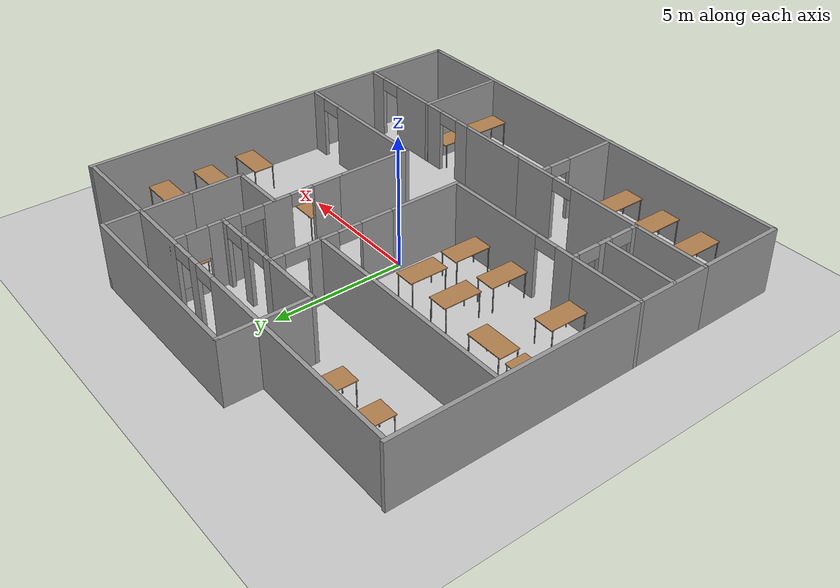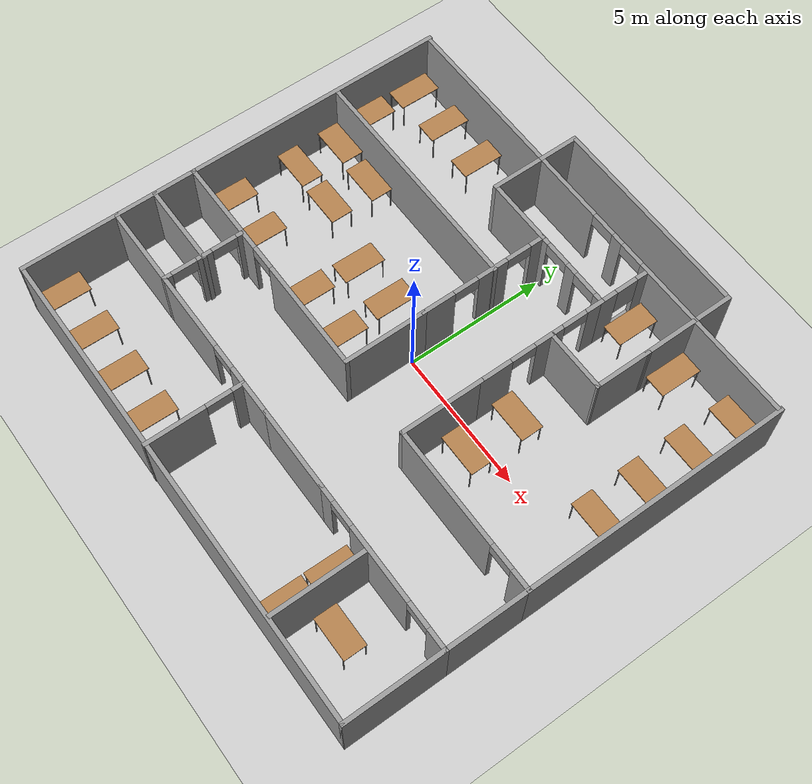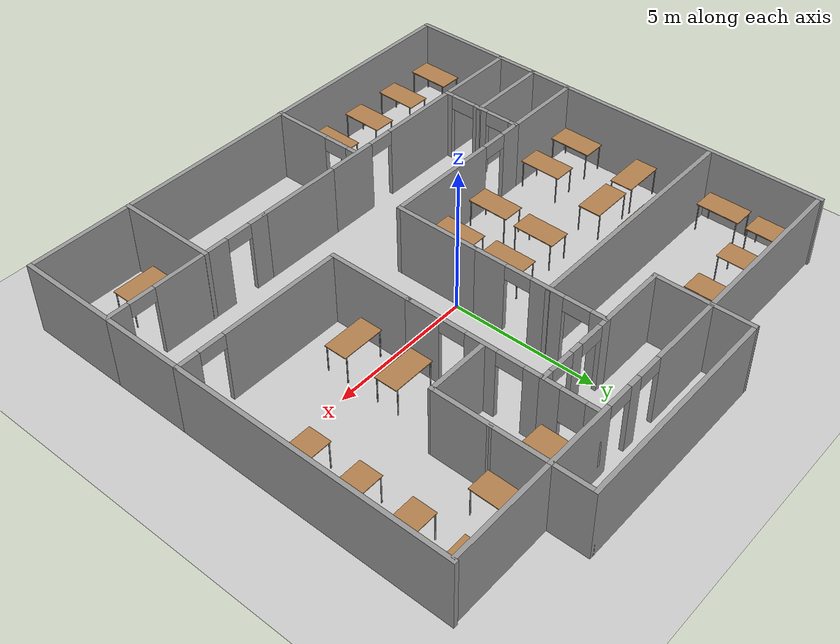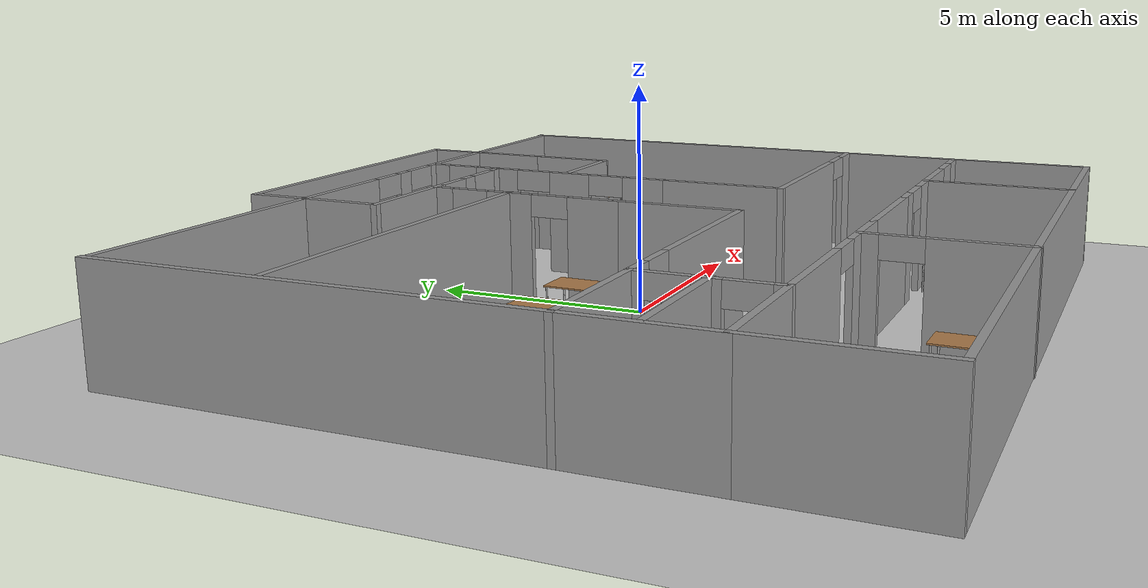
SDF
<sdf version="1.7">
 <world name="default">
  <light name="sun" type="directional">
   <pose>0 0 10 0 -0 0</pose>
   <diffuse>0.8 0.8 0.8 1</diffuse>
   <specular>0.2 0.2 0.2 1</specular>
   <attenuation>
    <range>1000</range>
    <constant>0.9</constant>
    <linear>0.01</linear>
    <quadratic>0.001</quadratic>
   </attenuation>
   <direction>-0.5 0.1 -0.9</direction>
   <spot><inner_angle>0</inner_angle><outer_angle>0</outer_angle><falloff>0</falloff></spot>
  </light>
  <model name="ground_plane">
   <static>1</static>
   <link name="link">
    <collision name="collision">
     <geometry><plane><normal>0 0 1</normal><size>100 100</size></plane></geometry>
     <surface><friction><ode><mu>100</mu><mu2>50</mu2></ode></friction></surface>
    </collision>
    <visual name="visual">
     <cast_shadows>0</cast_shadows>
     <geometry><plane><normal>0 0 1</normal><size>100 100</size></plane></geometry>
     <material>
      <script><uri>file://media/materials/scripts/gazebo.material</uri><name>Gazebo/Grey</name></script>
     </material>
    </visual>
   </link>
  </model>
  <gravity>0 0 -9.8</gravity>
  <magnetic_field>6e-06 2.3e-05 -4.2e-05</magnetic_field>
  <atmosphere type="adiabatic"/>
  <physics name="default_physics" default="0" type="ode">
   <max_step_size>0.001</max_step_size>
   <real_time_factor>1</real_time_factor>
   <real_time_update_rate>1000</real_time_update_rate>
  </physics>
  <scene><ambient>0.4 0.4 0.4 1</ambient><background>0.7 0.7 0.7 1</background><shadows>1</shadows></scene>
  <spherical_coordinates>
   <surface_model>EARTH_WGS84</surface_model>
   <latitude_deg>0</latitude_deg>
   <longitude_deg>0</longitude_deg>
   <elevation>0</elevation>
   <heading_deg>0</heading_deg>
  </spherical_coordinates>
  <model name="office">
   <pose>-0.02839 -0.13951 0 0 -0 0</pose>
   <link name="Wall_100">
    <collision name="Wall_100_Collision">
     <geometry><box><size>3 0.15 2.5</size></box></geometry>
     <pose>0 0 1.25 0 -0 0</pose>
    </collision>
    <visual name="Wall_100_Visual">
     <pose>0 0 1.25 0 -0 0</pose>
     <geometry><box><size>3 0.15 2.5</size></box></geometry>
     <material>
      <script><uri>file://media/materials/scripts/gazebo.material</uri><name>Gazebo/Grey</name></script>
      <ambient>1 1 1 1</ambient>
     </material>
     <meta><layer>0</layer></meta>
    </visual>
    <pose>-7.10827 -3.66762 0 0 -0 3.14159</pose>
   </link>
   <link name="Wall_11">
    <pose>2.725 2.93539 0 0 -0 1.5708</pose>
    <visual name="Wall_11_Visual_0">
     <pose>-1.77172 0 1.25 0 -0 0</pose>
     <geometry><box><size>1.20655 0.15 2.5</size></box></geometry>
     <material>
      <script><uri>file://media/materials/scripts/gazebo.material</uri><name>Gazebo/Grey</name></script>
      <ambient>1 1 1 1</ambient>
     </material>
     <meta><layer>0</layer></meta>
    </visual>
    <collision name="Wall_11_Collision_0">
     <geometry><box><size>1.20655 0.15 2.5</size></box></geometry>
     <pose>-1.77172 0 1.25 0 -0 0</pose>
    </collision>
    <visual name="Wall_11_Visual_1">
     <pose>0.268144 0 1.25 0 -0 0</pose>
     <geometry><box><size>1.07319 0.15 2.5</size></box></geometry>
     <material>
      <script><uri>file://media/materials/scripts/gazebo.material</uri><name>Gazebo/Grey</name></script>
      <ambient>1 1 1 1</ambient>
     </material>
     <meta><layer>0</layer></meta>
    </visual>
    <collision name="Wall_11_Collision_1">
     <geometry><box><size>1.07319 0.15 2.5</size></box></geometry>
     <pose>0.268144 0 1.25 0 -0 0</pose>
    </collision>
    <visual name="Wall_11_Visual_2">
     <pose>2.03987 0 1.25 0 -0 0</pose>
     <geometry><box><size>0.670261 0.15 2.5</size></box></geometry>
     <material>
      <script><uri>file://media/materials/scripts/gazebo.material</uri><name>Gazebo/Grey</name></script>
      <ambient>1 1 1 1</ambient>
     </material>
     <meta><layer>0</layer></meta>
    </visual>
    <collision name="Wall_11_Collision_2">
     <geometry><box><size>0.670261 0.15 2.5</size></box></geometry>
     <pose>2.03987 0 1.25 0 -0 0</pose>
    </collision>
    <visual name="Wall_11_Visual_3">
     <pose>-0.71845 0 2.25 0 -0 0</pose>
     <geometry><box><size>0.9 0.15 0.5</size></box></geometry>
     <material>
      <script><uri>file://media/materials/scripts/gazebo.material</uri><name>Gazebo/Grey</name></script>
      <ambient>1 1 1 1</ambient>
     </material>
     <meta><layer>0</layer></meta>
    </visual>
    <collision name="Wall_11_Collision_3">
     <geometry><box><size>0.9 0.15 0.5</size></box></geometry>
     <pose>-0.71845 0 2.25 0 -0 0</pose>
    </collision>
    <visual name="Wall_11_Visual_4">
     <pose>1.25474 0 2.25 0 -0 0</pose>
     <geometry><box><size>0.9 0.15 0.5</size></box></geometry>
     <material>
      <script><uri>file://media/materials/scripts/gazebo.material</uri><name>Gazebo/Grey</name></script>
      <ambient>1 1 1 1</ambient>
     </material>
     <meta><layer>0</layer></meta>
    </visual>
    <collision name="Wall_11_Collision_4">
     <geometry><box><size>0.9 0.15 0.5</size></box></geometry>
     <pose>1.25474 0 2.25 0 -0 0</pose>
    </collision>
   </link>
   <link name="Wall_12">
    <pose>1.3 5.23539 0 0 -0 3.14159</pose>
    <visual name="Wall_12_Visual_0">
     <pose>-1.3013 0 1.25 0 -0 0</pose>
     <geometry><box><size>0.397395 0.15 2.5</size></box></geometry>
     <material>
      <script><uri>file://media/materials/scripts/gazebo.material</uri><name>Gazebo/Grey</name></script>
      <ambient>1 1 1 1</ambient>
     </material>
     <meta><layer>0</layer></meta>
    </visual>
    <collision name="Wall_12_Collision_0">
     <geometry><box><size>0.397395 0.15 2.5</size></box></geometry>
     <pose>-1.3013 0 1.25 0 -0 0</pose>
    </collision>
    <visual name="Wall_12_Visual_1">
     <pose>0.006617 0 1.25 0 -0 0</pose>
     <geometry><box><size>0.418445 0.15 2.5</size></box></geometry>
     <material>
      <script><uri>file://media/materials/scripts/gazebo.material</uri><name>Gazebo/Grey</name></script>
      <ambient>1 1 1 1</ambient>
     </material>
     <meta><layer>0</layer></meta>
    </visual>
    <collision name="Wall_12_Collision_1">
     <geometry><box><size>0.418445 0.15 2.5</size></box></geometry>
     <pose>0.006617 0 1.25 0 -0 0</pose>
    </collision>
    <visual name="Wall_12_Visual_2">
     <pose>1.30792 0 1.25 0 -0 0</pose>
     <geometry><box><size>0.384161 0.15 2.5</size></box></geometry>
     <material>
      <script><uri>file://media/materials/scripts/gazebo.material</uri><name>Gazebo/Grey</name></script>
      <ambient>1 1 1 1</ambient>
     </material>
     <meta><layer>0</layer></meta>
    </visual>
    <collision name="Wall_12_Collision_2">
     <geometry><box><size>0.384161 0.15 2.5</size></box></geometry>
     <pose>1.30792 0 1.25 0 -0 0</pose>
    </collision>
    <visual name="Wall_12_Visual_3">
     <pose>-0.652605 0 2.25 0 -0 0</pose>
     <geometry><box><size>0.9 0.15 0.5</size></box></geometry>
     <material>
      <script><uri>file://media/materials/scripts/gazebo.material</uri><name>Gazebo/Grey</name></script>
      <ambient>1 1 1 1</ambient>
     </material>
     <meta><layer>0</layer></meta>
    </visual>
    <collision name="Wall_12_Collision_3">
     <geometry><box><size>0.9 0.15 0.5</size></box></geometry>
     <pose>-0.652605 0 2.25 0 -0 0</pose>
    </collision>
    <visual name="Wall_12_Visual_4">
     <pose>0.665839 0 2.25 0 -0 0</pose>
     <geometry><box><size>0.9 0.15 0.5</size></box></geometry>
     <material>
      <script><uri>file://media/materials/scripts/gazebo.material</uri><name>Gazebo/Grey</name></script>
      <ambient>1 1 1 1</ambient>
     </material>
     <meta><layer>0</layer></meta>
    </visual>
    <collision name="Wall_12_Collision_4">
     <geometry><box><size>0.9 0.15 0.5</size></box></geometry>
     <pose>0.665839 0 2.25 0 -0 0</pose>
    </collision>
   </link>
   <link name="Wall_13">
    <pose>-0.125 2.93539 0 0 -0 -1.5708</pose>
    <visual name="Wall_13_Visual_0">
     <pose>-2.08548 0 1.25 0 -0 0</pose>
     <geometry><box><size>0.579043 0.15 2.5</size></box></geometry>
     <material>
      <script><uri>file://media/materials/scripts/gazebo.material</uri><name>Gazebo/Grey</name></script>
      <ambient>1 1 1 1</ambient>
     </material>
     <meta><layer>0</layer></meta>
    </visual>
    <collision name="Wall_13_Collision_0">
     <geometry><box><size>0.579043 0.15 2.5</size></box></geometry>
     <pose>-2.08548 0 1.25 0 -0 0</pose>
    </collision>
    <visual name="Wall_13_Visual_1">
     <pose>-0.329311 0 1.25 0 -0 0</pose>
     <geometry><box><size>1.13329 0.15 2.5</size></box></geometry>
     <material>
      <script><uri>file://media/materials/scripts/gazebo.material</uri><name>Gazebo/Grey</name></script>
      <ambient>1 1 1 1</ambient>
     </material>
     <meta><layer>0</layer></meta>
    </visual>
    <collision name="Wall_13_Collision_1">
     <geometry><box><size>1.13329 0.15 2.5</size></box></geometry>
     <pose>-0.329311 0 1.25 0 -0 0</pose>
    </collision>
    <visual name="Wall_13_Visual_2">
     <pose>1.75617 0 1.25 0 -0 0</pose>
     <geometry><box><size>1.23766 0.15 2.5</size></box></geometry>
     <material>
      <script><uri>file://media/materials/scripts/gazebo.material</uri><name>Gazebo/Grey</name></script>
      <ambient>1 1 1 1</ambient>
     </material>
     <meta><layer>0</layer></meta>
    </visual>
    <collision name="Wall_13_Collision_2">
     <geometry><box><size>1.23766 0.15 2.5</size></box></geometry>
     <pose>1.75617 0 1.25 0 -0 0</pose>
    </collision>
    <visual name="Wall_13_Visual_3">
     <pose>-1.34596 0 2.25 0 -0 0</pose>
     <geometry><box><size>0.9 0.15 0.5</size></box></geometry>
     <material>
      <script><uri>file://media/materials/scripts/gazebo.material</uri><name>Gazebo/Grey</name></script>
      <ambient>1 1 1 1</ambient>
     </material>
     <meta><layer>0</layer></meta>
    </visual>
    <collision name="Wall_13_Collision_3">
     <geometry><box><size>0.9 0.15 0.5</size></box></geometry>
     <pose>-1.34596 0 2.25 0 -0 0</pose>
    </collision>
    <visual name="Wall_13_Visual_4">
     <pose>0.687336 0 2.25 0 -0 0</pose>
     <geometry><box><size>0.9 0.15 0.5</size></box></geometry>
     <material>
      <script><uri>file://media/materials/scripts/gazebo.material</uri><name>Gazebo/Grey</name></script>
      <ambient>1 1 1 1</ambient>
     </material>
     <meta><layer>0</layer></meta>
    </visual>
    <collision name="Wall_13_Collision_4">
     <geometry><box><size>0.9 0.15 0.5</size></box></geometry>
     <pose>0.687336 0 2.25 0 -0 0</pose>
    </collision>
   </link>
   <link name="Wall_15">
    <collision name="Wall_15_Collision">
     <geometry><box><size>2.5 0.15 2.5</size></box></geometry>
     <pose>0 0 1.25 0 -0 0</pose>
    </collision>
    <visual name="Wall_15_Visual">
     <pose>0 0 1.25 0 -0 0</pose>
     <geometry><box><size>2.5 0.15 2.5</size></box></geometry>
     <material>
      <script><uri>file://media/materials/scripts/gazebo.material</uri><name>Gazebo/Grey</name></script>
      <ambient>1 1 1 1</ambient>
     </material>
     <meta><layer>0</layer></meta>
    </visual>
    <pose>-1.3 5.23539 0 0 -0 3.14159</pose>
   </link>
   <link name="Wall_25">
    <collision name="Wall_25_Collision">
     <geometry><box><size>2 0.15 2.5</size></box></geometry>
     <pose>0 0 1.25 0 -0 0</pose>
    </collision>
    <visual name="Wall_25_Visual">
     <pose>0 0 1.25 0 -0 0</pose>
     <geometry><box><size>2 0.15 2.5</size></box></geometry>
     <material>
      <script><uri>file://media/materials/scripts/gazebo.material</uri><name>Gazebo/Grey</name></script>
      <ambient>1 1 1 1</ambient>
     </material>
     <meta><layer>0</layer></meta>
    </visual>
    <pose>-2.475 6.16039 0 0 -0 1.5708</pose>
   </link>
   <link name="Wall_26">
    <pose>1.2 7.08539 0 0 -0 0</pose>
    <visual name="Wall_26_Visual_0">
     <pose>-2.38462 0 1.25 0 -0 0</pose>
     <geometry><box><size>2.73077 0.15 2.5</size></box></geometry>
     <material>
      <script><uri>file://media/materials/scripts/gazebo.material</uri><name>Gazebo/Grey</name></script>
      <ambient>1 1 1 1</ambient>
     </material>
     <meta><layer>0</layer></meta>
    </visual>
    <collision name="Wall_26_Collision_0">
     <geometry><box><size>2.73077 0.15 2.5</size></box></geometry>
     <pose>-2.38462 0 1.25 0 -0 0</pose>
    </collision>
    <visual name="Wall_26_Visual_1">
     <pose>0.103755 0 1.25 0 -0 0</pose>
     <geometry><box><size>0.44597 0.15 2.5</size></box></geometry>
     <material>
      <script><uri>file://media/materials/scripts/gazebo.material</uri><name>Gazebo/Grey</name></script>
      <ambient>1 1 1 1</ambient>
     </material>
     <meta><layer>0</layer></meta>
    </visual>
    <collision name="Wall_26_Collision_1">
     <geometry><box><size>0.44597 0.15 2.5</size></box></geometry>
     <pose>0.103755 0 1.25 0 -0 0</pose>
    </collision>
    <visual name="Wall_26_Visual_2">
     <pose>2.48837 0 1.25 0 -0 0</pose>
     <geometry><box><size>2.52326 0.15 2.5</size></box></geometry>
     <material>
      <script><uri>file://media/materials/scripts/gazebo.material</uri><name>Gazebo/Grey</name></script>
      <ambient>1 1 1 1</ambient>
     </material>
     <meta><layer>0</layer></meta>
    </visual>
    <collision name="Wall_26_Collision_2">
     <geometry><box><size>2.52326 0.15 2.5</size></box></geometry>
     <pose>2.48837 0 1.25 0 -0 0</pose>
    </collision>
    <visual name="Wall_26_Visual_3">
     <pose>-0.56923 0 2.25 0 -0 0</pose>
     <geometry><box><size>0.9 0.15 0.5</size></box></geometry>
     <material>
      <script><uri>file://media/materials/scripts/gazebo.material</uri><name>Gazebo/Grey</name></script>
      <ambient>1 1 1 1</ambient>
     </material>
     <meta><layer>0</layer></meta>
    </visual>
    <collision name="Wall_26_Collision_3">
     <geometry><box><size>0.9 0.15 0.5</size></box></geometry>
     <pose>-0.56923 0 2.25 0 -0 0</pose>
    </collision>
    <visual name="Wall_26_Visual_4">
     <pose>0.77674 0 2.25 0 -0 0</pose>
     <geometry><box><size>0.9 0.15 0.5</size></box></geometry>
     <material>
      <script><uri>file://media/materials/scripts/gazebo.material</uri><name>Gazebo/Grey</name></script>
      <ambient>1 1 1 1</ambient>
     </material>
     <meta><layer>0</layer></meta>
    </visual>
    <collision name="Wall_26_Collision_4">
     <geometry><box><size>0.9 0.15 0.5</size></box></geometry>
     <pose>0.77674 0 2.25 0 -0 0</pose>
    </collision>
   </link>
   <link name="Wall_27">
    <collision name="Wall_27_Collision">
     <geometry><box><size>2 0.15 2.5</size></box></geometry>
     <pose>0 0 1.25 0 -0 0</pose>
    </collision>
    <visual name="Wall_27_Visual">
     <pose>0 0 1.25 0 -0 0</pose>
     <geometry><box><size>2 0.15 2.5</size></box></geometry>
     <material>
      <script><uri>file://media/materials/scripts/gazebo.material</uri><name>Gazebo/Grey</name></script>
      <ambient>1 1 1 1</ambient>
     </material>
     <meta><layer>0</layer></meta>
    </visual>
    <pose>4.875 6.16039 0 0 -0 -1.5708</pose>
   </link>
   <link name="Wall_29">
    <collision name="Wall_29_Collision">
     <geometry><box><size>1.5 0.15 2.5</size></box></geometry>
     <pose>0 0 1.25 0 -0 0</pose>
    </collision>
    <visual name="Wall_29_Visual">
     <pose>0 0 1.25 0 -0 0</pose>
     <geometry><box><size>1.5 0.15 2.5</size></box></geometry>
     <material>
      <script><uri>file://media/materials/scripts/gazebo.material</uri><name>Gazebo/Grey</name></script>
      <ambient>1 1 1 1</ambient>
     </material>
     <meta><layer>0</layer></meta>
    </visual>
    <pose>-2.475 7.76039 0 0 -0 1.5708</pose>
   </link>
   <link name="Wall_30">
    <collision name="Wall_30_Collision">
     <geometry><box><size>7.5 0.15 2.5</size></box></geometry>
     <pose>0 0 1.25 0 -0 0</pose>
    </collision>
    <visual name="Wall_30_Visual">
     <pose>0 0 1.25 0 -0 0</pose>
     <geometry><box><size>7.5 0.15 2.5</size></box></geometry>
     <material>
      <script><uri>file://media/materials/scripts/gazebo.material</uri><name>Gazebo/Grey</name></script>
      <ambient>1 1 1 1</ambient>
     </material>
     <meta><layer>0</layer></meta>
    </visual>
    <pose>1.2 8.43539 0 0 -0 0</pose>
   </link>
   <link name="Wall_31">
    <collision name="Wall_31_Collision">
     <geometry><box><size>1.5 0.15 2.5</size></box></geometry>
     <pose>0 0 1.25 0 -0 0</pose>
    </collision>
    <visual name="Wall_31_Visual">
     <pose>0 0 1.25 0 -0 0</pose>
     <geometry><box><size>1.5 0.15 2.5</size></box></geometry>
     <material>
      <script><uri>file://media/materials/scripts/gazebo.material</uri><name>Gazebo/Grey</name></script>
      <ambient>1 1 1 1</ambient>
     </material>
     <meta><layer>0</layer></meta>
    </visual>
    <pose>4.875 7.76039 0 0 -0 -1.5708</pose>
   </link>
   <link name="Wall_35">
    <pose>2.725 6.16039 0 0 -0 1.5708</pose>
    <visual name="Wall_35_Visual_0">
     <pose>-0.673622 0 1.25 0 -0 0</pose>
     <geometry><box><size>0.652756 0.15 2.5</size></box></geometry>
     <material>
      <script><uri>file://media/materials/scripts/gazebo.material</uri><name>Gazebo/Grey</name></script>
      <ambient>1 1 1 1</ambient>
     </material>
     <meta><layer>0</layer></meta>
    </visual>
    <collision name="Wall_35_Collision_0">
     <geometry><box><size>0.652756 0.15 2.5</size></box></geometry>
     <pose>-0.673622 0 1.25 0 -0 0</pose>
    </collision>
    <visual name="Wall_35_Visual_1">
     <pose>0.326378 0 0.25 0 -0 0</pose>
     <geometry><box><size>1.34724 0.15 0.5</size></box></geometry>
     <material>
      <script><uri>file://media/materials/scripts/gazebo.material</uri><name>Gazebo/Grey</name></script>
      <ambient>1 1 1 1</ambient>
     </material>
     <meta><layer>0</layer></meta>
    </visual>
    <collision name="Wall_35_Collision_1">
     <geometry><box><size>1.34724 0.15 0.5</size></box></geometry>
     <pose>0.326378 0 0.25 0 -0 0</pose>
    </collision>
    <visual name="Wall_35_Visual_2">
     <pose>0.726378 0 1.5 0 -0 0</pose>
     <geometry><box><size>0.547244 0.15 2</size></box></geometry>
     <material>
      <script><uri>file://media/materials/scripts/gazebo.material</uri><name>Gazebo/Grey</name></script>
      <ambient>1 1 1 1</ambient>
     </material>
     <meta><layer>0</layer></meta>
    </visual>
    <collision name="Wall_35_Collision_2">
     <geometry><box><size>0.547244 0.15 2</size></box></geometry>
     <pose>0.726378 0 1.5 0 -0 0</pose>
    </collision>
    <visual name="Wall_35_Visual_3">
     <pose>0.052756 0 1.9 0 -0 0</pose>
     <geometry><box><size>0.8 0.15 1.2</size></box></geometry>
     <material>
      <script><uri>file://media/materials/scripts/gazebo.material</uri><name>Gazebo/Grey</name></script>
      <ambient>1 1 1 1</ambient>
     </material>
     <meta><layer>0</layer></meta>
    </visual>
    <collision name="Wall_35_Collision_3">
     <geometry><box><size>0.8 0.15 1.2</size></box></geometry>
     <pose>0.052756 0 1.9 0 -0 0</pose>
    </collision>
   </link>
   <link name="Wall_38">
    <collision name="Wall_38_Collision">
     <geometry><box><size>3 0.15 2.5</size></box></geometry>
     <pose>0 0 1.25 0 -0 0</pose>
    </collision>
    <visual name="Wall_38_Visual">
     <pose>0 0 1.25 0 -0 0</pose>
     <geometry><box><size>3 0.15 2.5</size></box></geometry>
     <material>
      <script><uri>file://media/materials/scripts/gazebo.material</uri><name>Gazebo/Grey</name></script>
      <ambient>1 1 1 1</ambient>
     </material>
     <meta><layer>0</layer></meta>
    </visual>
    <pose>-0.125 -0.789611 0 0 -0 -1.5708</pose>
   </link>
   <link name="Wall_40">
    <collision name="Wall_40_Collision">
     <geometry><box><size>3 0.15 2.5</size></box></geometry>
     <pose>0 0 1.25 0 -0 0</pose>
    </collision>
    <visual name="Wall_40_Visual">
     <pose>0 0 1.25 0 -0 0</pose>
     <geometry><box><size>3 0.15 2.5</size></box></geometry>
     <material>
      <script><uri>file://media/materials/scripts/gazebo.material</uri><name>Gazebo/Grey</name></script>
      <ambient>1 1 1 1</ambient>
     </material>
     <meta><layer>0</layer></meta>
    </visual>
    <pose>2.725 -0.789611 0 0 -0 1.5708</pose>
   </link>
   <link name="Wall_43">
    <collision name="Wall_43_Collision">
     <geometry><box><size>3 0.15 2.5</size></box></geometry>
     <pose>0 0 1.25 0 -0 0</pose>
    </collision>
    <visual name="Wall_43_Visual">
     <pose>0 0 1.25 0 -0 0</pose>
     <geometry><box><size>3 0.15 2.5</size></box></geometry>
     <material>
      <script><uri>file://media/materials/scripts/gazebo.material</uri><name>Gazebo/Grey</name></script>
      <ambient>1 1 1 1</ambient>
     </material>
     <meta><layer>0</layer></meta>
    </visual>
    <pose>1.3 -5.06461 0 0 -0 0</pose>
   </link>
   <link name="Wall_45">
    <pose>5.65 -2.21461 0 0 -0 0</pose>
    <visual name="Wall_45_Visual_0">
     <pose>-0.855194 0 1.25 0 -0 0</pose>
     <geometry><box><size>4.28961 0.15 2.5</size></box></geometry>
     <material>
      <script><uri>file://media/materials/scripts/gazebo.material</uri><name>Gazebo/Grey</name></script>
      <ambient>1 1 1 1</ambient>
     </material>
     <meta><layer>0</layer></meta>
    </visual>
    <collision name="Wall_45_Collision_0">
     <geometry><box><size>4.28961 0.15 2.5</size></box></geometry>
     <pose>-0.855194 0 1.25 0 -0 0</pose>
    </collision>
    <visual name="Wall_45_Visual_1">
     <pose>2.59481 0 1.25 0 -0 0</pose>
     <geometry><box><size>0.810387 0.15 2.5</size></box></geometry>
     <material>
      <script><uri>file://media/materials/scripts/gazebo.material</uri><name>Gazebo/Grey</name></script>
      <ambient>1 1 1 1</ambient>
     </material>
     <meta><layer>0</layer></meta>
    </visual>
    <collision name="Wall_45_Collision_1">
     <geometry><box><size>0.810387 0.15 2.5</size></box></geometry>
     <pose>2.59481 0 1.25 0 -0 0</pose>
    </collision>
    <visual name="Wall_45_Visual_2">
     <pose>1.73961 0 2.25 0 -0 0</pose>
     <geometry><box><size>0.9 0.15 0.5</size></box></geometry>
     <material>
      <script><uri>file://media/materials/scripts/gazebo.material</uri><name>Gazebo/Grey</name></script>
      <ambient>1 1 1 1</ambient>
     </material>
     <meta><layer>0</layer></meta>
    </visual>
    <collision name="Wall_45_Collision_2">
     <geometry><box><size>0.9 0.15 0.5</size></box></geometry>
     <pose>1.73961 0 2.25 0 -0 0</pose>
    </collision>
   </link>
   <link name="Wall_46">
    <collision name="Wall_46_Collision">
     <geometry><box><size>3 0.15 2.5</size></box></geometry>
     <pose>0 0 1.25 0 -0 0</pose>
    </collision>
    <visual name="Wall_46_Visual">
     <pose>0 0 1.25 0 -0 0</pose>
     <geometry><box><size>3 0.15 2.5</size></box></geometry>
     <material>
      <script><uri>file://media/materials/scripts/gazebo.material</uri><name>Gazebo/Grey</name></script>
      <ambient>1 1 1 1</ambient>
     </material>
     <meta><layer>0</layer></meta>
    </visual>
    <pose>8.575 -3.63961 0 0 -0 -1.5708</pose>
   </link>
   <link name="Wall_47">
    <pose>5.65 -5.06461 0 0 -0 3.14159</pose>
    <visual name="Wall_47_Visual_0">
     <pose>-2.58723 0 1.25 0 -0 0</pose>
     <geometry><box><size>0.825548 0.15 2.5</size></box></geometry>
     <material>
      <script><uri>file://media/materials/scripts/gazebo.material</uri><name>Gazebo/Grey</name></script>
      <ambient>1 1 1 1</ambient>
     </material>
     <meta><layer>0</layer></meta>
    </visual>
    <collision name="Wall_47_Collision_0">
     <geometry><box><size>0.825548 0.15 2.5</size></box></geometry>
     <pose>-2.58723 0 1.25 0 -0 0</pose>
    </collision>
    <visual name="Wall_47_Visual_1">
     <pose>0.08609 0 1.25 0 -0 0</pose>
     <geometry><box><size>2.72108 0.15 2.5</size></box></geometry>
     <material>
      <script><uri>file://media/materials/scripts/gazebo.material</uri><name>Gazebo/Grey</name></script>
      <ambient>1 1 1 1</ambient>
     </material>
     <meta><layer>0</layer></meta>
    </visual>
    <collision name="Wall_47_Collision_1">
     <geometry><box><size>2.72108 0.15 2.5</size></box></geometry>
     <pose>0.08609 0 1.25 0 -0 0</pose>
    </collision>
    <visual name="Wall_47_Visual_2">
     <pose>2.67332 0 1.25 0 -0 0</pose>
     <geometry><box><size>0.653368 0.15 2.5</size></box></geometry>
     <material>
      <script><uri>file://media/materials/scripts/gazebo.material</uri><name>Gazebo/Grey</name></script>
      <ambient>1 1 1 1</ambient>
     </material>
     <meta><layer>0</layer></meta>
    </visual>
    <collision name="Wall_47_Collision_2">
     <geometry><box><size>0.653368 0.15 2.5</size></box></geometry>
     <pose>2.67332 0 1.25 0 -0 0</pose>
    </collision>
    <visual name="Wall_47_Visual_3">
     <pose>-1.72445 0 2.25 0 -0 0</pose>
     <geometry><box><size>0.9 0.15 0.5</size></box></geometry>
     <material>
      <script><uri>file://media/materials/scripts/gazebo.material</uri><name>Gazebo/Grey</name></script>
      <ambient>1 1 1 1</ambient>
     </material>
     <meta><layer>0</layer></meta>
    </visual>
    <collision name="Wall_47_Collision_3">
     <geometry><box><size>0.9 0.15 0.5</size></box></geometry>
     <pose>-1.72445 0 2.25 0 -0 0</pose>
    </collision>
    <visual name="Wall_47_Visual_4">
     <pose>1.89663 0 2.25 0 -0 0</pose>
     <geometry><box><size>0.9 0.15 0.5</size></box></geometry>
     <material>
      <script><uri>file://media/materials/scripts/gazebo.material</uri><name>Gazebo/Grey</name></script>
      <ambient>1 1 1 1</ambient>
     </material>
     <meta><layer>0</layer></meta>
    </visual>
    <collision name="Wall_47_Collision_4">
     <geometry><box><size>0.9 0.15 0.5</size></box></geometry>
     <pose>1.89663 0 2.25 0 -0 0</pose>
    </collision>
   </link>
   <link name="Wall_49">
    <pose>-2.925 -2.21461 0 0 -0 3.14159</pose>
    <visual name="Wall_49_Visual_0">
     <pose>-0.830299 0 1.25 0 -0 0</pose>
     <geometry><box><size>4.0894 0.15 2.5</size></box></geometry>
     <material>
      <script><uri>file://media/materials/scripts/gazebo.material</uri><name>Gazebo/Grey</name></script>
      <ambient>1 1 1 1</ambient>
     </material>
     <meta><layer>0</layer></meta>
    </visual>
    <collision name="Wall_49_Collision_0">
     <geometry><box><size>4.0894 0.15 2.5</size></box></geometry>
     <pose>-0.830299 0 1.25 0 -0 0</pose>
    </collision>
    <visual name="Wall_49_Visual_1">
     <pose>2.4947 0 1.25 0 -0 0</pose>
     <geometry><box><size>0.760599 0.15 2.5</size></box></geometry>
     <material>
      <script><uri>file://media/materials/scripts/gazebo.material</uri><name>Gazebo/Grey</name></script>
      <ambient>1 1 1 1</ambient>
     </material>
     <meta><layer>0</layer></meta>
    </visual>
    <collision name="Wall_49_Collision_1">
     <geometry><box><size>0.760599 0.15 2.5</size></box></geometry>
     <pose>2.4947 0 1.25 0 -0 0</pose>
    </collision>
    <visual name="Wall_49_Visual_2">
     <pose>1.6644 0 2.25 0 -0 0</pose>
     <geometry><box><size>0.9 0.15 0.5</size></box></geometry>
     <material>
      <script><uri>file://media/materials/scripts/gazebo.material</uri><name>Gazebo/Grey</name></script>
      <ambient>1 1 1 1</ambient>
     </material>
     <meta><layer>0</layer></meta>
    </visual>
    <collision name="Wall_49_Collision_2">
     <geometry><box><size>0.9 0.15 0.5</size></box></geometry>
     <pose>1.6644 0 2.25 0 -0 0</pose>
    </collision>
   </link>
   <link name="Wall_52">
    <pose>-2.925 -5.06461 0 0 -0 3.14159</pose>
    <visual name="Wall_52_Visual_0">
     <pose>-1.93486 0 1.25 0 -0 0</pose>
     <geometry><box><size>1.88028 0.15 2.5</size></box></geometry>
     <material>
      <script><uri>file://media/materials/scripts/gazebo.material</uri><name>Gazebo/Grey</name></script>
      <ambient>1 1 1 1</ambient>
     </material>
     <meta><layer>0</layer></meta>
    </visual>
    <collision name="Wall_52_Collision_0">
     <geometry><box><size>1.88028 0.15 2.5</size></box></geometry>
     <pose>-1.93486 0 1.25 0 -0 0</pose>
    </collision>
    <visual name="Wall_52_Visual_1">
     <pose>1.39014 0 1.25 0 -0 0</pose>
     <geometry><box><size>2.96972 0.15 2.5</size></box></geometry>
     <material>
      <script><uri>file://media/materials/scripts/gazebo.material</uri><name>Gazebo/Grey</name></script>
      <ambient>1 1 1 1</ambient>
     </material>
     <meta><layer>0</layer></meta>
    </visual>
    <collision name="Wall_52_Collision_1">
     <geometry><box><size>2.96972 0.15 2.5</size></box></geometry>
     <pose>1.39014 0 1.25 0 -0 0</pose>
    </collision>
    <visual name="Wall_52_Visual_2">
     <pose>-0.544716 0 2.25 0 -0 0</pose>
     <geometry><box><size>0.9 0.15 0.5</size></box></geometry>
     <material>
      <script><uri>file://media/materials/scripts/gazebo.material</uri><name>Gazebo/Grey</name></script>
      <ambient>1 1 1 1</ambient>
     </material>
     <meta><layer>0</layer></meta>
    </visual>
    <collision name="Wall_52_Collision_2">
     <geometry><box><size>0.9 0.15 0.5</size></box></geometry>
     <pose>-0.544716 0 2.25 0 -0 0</pose>
    </collision>
   </link>
   <link name="Wall_53">
    <pose>-5.725 -3.63961 0 0 -0 1.5708</pose>
    <visual name="Wall_53_Visual_0">
     <pose>-1.33679 0 1.25 0 -0 0</pose>
     <geometry><box><size>0.326418 0.15 2.5</size></box></geometry>
     <material>
      <script><uri>file://media/materials/scripts/gazebo.material</uri><name>Gazebo/Grey</name></script>
      <ambient>1 1 1 1</ambient>
     </material>
     <meta><layer>0</layer></meta>
    </visual>
    <collision name="Wall_53_Collision_0">
     <geometry><box><size>0.326418 0.15 2.5</size></box></geometry>
     <pose>-1.33679 0 1.25 0 -0 0</pose>
    </collision>
    <visual name="Wall_53_Visual_1">
     <pose>0.002683 0 1.25 0 -0 0</pose>
     <geometry><box><size>0.55253 0.15 2.5</size></box></geometry>
     <material>
      <script><uri>file://media/materials/scripts/gazebo.material</uri><name>Gazebo/Grey</name></script>
      <ambient>1 1 1 1</ambient>
     </material>
     <meta><layer>0</layer></meta>
    </visual>
    <collision name="Wall_53_Collision_1">
     <geometry><box><size>0.55253 0.15 2.5</size></box></geometry>
     <pose>0.002683 0 1.25 0 -0 0</pose>
    </collision>
    <visual name="Wall_53_Visual_2">
     <pose>1.33947 0 1.25 0 -0 0</pose>
     <geometry><box><size>0.321051 0.15 2.5</size></box></geometry>
     <material>
      <script><uri>file://media/materials/scripts/gazebo.material</uri><name>Gazebo/Grey</name></script>
      <ambient>1 1 1 1</ambient>
     </material>
     <meta><layer>0</layer></meta>
    </visual>
    <collision name="Wall_53_Collision_2">
     <geometry><box><size>0.321051 0.15 2.5</size></box></geometry>
     <pose>1.33947 0 1.25 0 -0 0</pose>
    </collision>
    <visual name="Wall_53_Visual_3">
     <pose>-0.723582 0 2.25 0 -0 0</pose>
     <geometry><box><size>0.9 0.15 0.5</size></box></geometry>
     <material>
      <script><uri>file://media/materials/scripts/gazebo.material</uri><name>Gazebo/Grey</name></script>
      <ambient>1 1 1 1</ambient>
     </material>
     <meta><layer>0</layer></meta>
    </visual>
    <collision name="Wall_53_Collision_3">
     <geometry><box><size>0.9 0.15 0.5</size></box></geometry>
     <pose>-0.723582 0 2.25 0 -0 0</pose>
    </collision>
    <visual name="Wall_53_Visual_4">
     <pose>0.728949 0 2.25 0 -0 0</pose>
     <geometry><box><size>0.9 0.15 0.5</size></box></geometry>
     <material>
      <script><uri>file://media/materials/scripts/gazebo.material</uri><name>Gazebo/Grey</name></script>
      <ambient>1 1 1 1</ambient>
     </material>
     <meta><layer>0</layer></meta>
    </visual>
    <collision name="Wall_53_Collision_4">
     <geometry><box><size>0.9 0.15 0.5</size></box></geometry>
     <pose>0.728949 0 2.25 0 -0 0</pose>
    </collision>
   </link>
   <link name="Wall_58">
    <collision name="Wall_58_Collision">
     <geometry><box><size>2.25 0.15 2.5</size></box></geometry>
     <pose>0 0 1.25 0 -0 0</pose>
    </collision>
    <visual name="Wall_58_Visual">
     <pose>0 0 1.25 0 -0 0</pose>
     <geometry><box><size>2.25 0.15 2.5</size></box></geometry>
     <material>
      <script><uri>file://media/materials/scripts/gazebo.material</uri><name>Gazebo/Grey</name></script>
      <ambient>1 1 1 1</ambient>
     </material>
     <meta><layer>0</layer></meta>
    </visual>
    <pose>3.81519 3.30301 0 0 -0 0</pose>
   </link>
   <link name="Wall_59">
    <collision name="Wall_59_Collision">
     <geometry><box><size>2.0824 0.15 2.5</size></box></geometry>
     <pose>0 0 1.25 0 -0 0</pose>
    </collision>
    <visual name="Wall_59_Visual">
     <pose>0 0 1.25 0 -0 0</pose>
     <geometry><box><size>2.0824 0.15 2.5</size></box></geometry>
     <material>
      <script><uri>file://media/materials/scripts/gazebo.material</uri><name>Gazebo/Grey</name></script>
      <ambient>1 1 1 1</ambient>
     </material>
     <meta><layer>0</layer></meta>
    </visual>
    <pose>4.8701 4.2692 0 0 -0 1.56572</pose>
   </link>
   <link name="Wall_69">
    <collision name="Wall_69_Collision">
     <geometry><box><size>3.75 0.15 2.5</size></box></geometry>
     <pose>0 0 1.25 0 -0 0</pose>
    </collision>
    <visual name="Wall_69_Visual">
     <pose>0 0 1.25 0 -0 0</pose>
     <geometry><box><size>3.75 0.15 2.5</size></box></geometry>
     <material>
      <script><uri>file://media/materials/scripts/gazebo.material</uri><name>Gazebo/Grey</name></script>
      <ambient>1 1 1 1</ambient>
     </material>
     <meta><layer>0</layer></meta>
    </visual>
    <pose>6.675 7.08539 0 0 -0 0</pose>
   </link>
   <link name="Wall_71">
    <collision name="Wall_71_Collision">
     <geometry><box><size>9.5 0.15 2.5</size></box></geometry>
     <pose>0 0 1.25 0 -0 0</pose>
    </collision>
    <visual name="Wall_71_Visual">
     <pose>0 0 1.25 0 -0 0</pose>
     <geometry><box><size>9.5 0.15 2.5</size></box></geometry>
     <material>
      <script><uri>file://media/materials/scripts/gazebo.material</uri><name>Gazebo/Grey</name></script>
      <ambient>1 1 1 1</ambient>
     </material>
     <meta><layer>0</layer></meta>
    </visual>
    <pose>8.575 2.46039 0 0 -0 1.5708</pose>
   </link>
   <link name="Wall_73">
    <collision name="Wall_73_Collision">
     <geometry><box><size>3.5 0.15 2.5</size></box></geometry>
     <pose>0 0 1.25 0 -0 0</pose>
    </collision>
    <visual name="Wall_73_Visual">
     <pose>0 0 1.25 0 -0 0</pose>
     <geometry><box><size>3.5 0.15 2.5</size></box></geometry>
     <material>
      <script><uri>file://media/materials/scripts/gazebo.material</uri><name>Gazebo/Grey</name></script>
      <ambient>1 1 1 1</ambient>
     </material>
     <meta><layer>0</layer></meta>
    </visual>
    <pose>8.575 -6.73961 0 0 -0 -1.5708</pose>
   </link>
   <link name="Wall_79">
    <collision name="Wall_79_Collision">
     <geometry><box><size>3 0.15 2.5</size></box></geometry>
     <pose>0 0 1.25 0 -0 0</pose>
    </collision>
    <visual name="Wall_79_Visual">
     <pose>0 0 1.25 0 -0 0</pose>
     <geometry><box><size>3 0.15 2.5</size></box></geometry>
     <material>
      <script><uri>file://media/materials/scripts/gazebo.material</uri><name>Gazebo/Grey</name></script>
      <ambient>1 1 1 1</ambient>
     </material>
     <meta><layer>0</layer></meta>
    </visual>
    <pose>-7.15 -2.21461 0 0 -0 3.14159</pose>
   </link>
   <link name="Wall_80">
    <collision name="Wall_80_Collision">
     <geometry><box><size>3 0.15 2.5</size></box></geometry>
     <pose>0 0 1.25 0 -0 0</pose>
    </collision>
    <visual name="Wall_80_Visual">
     <pose>0 0 1.25 0 -0 0</pose>
     <geometry><box><size>3 0.15 2.5</size></box></geometry>
     <material>
      <script><uri>file://media/materials/scripts/gazebo.material</uri><name>Gazebo/Grey</name></script>
      <ambient>1 1 1 1</ambient>
     </material>
     <meta><layer>0</layer></meta>
    </visual>
    <pose>-8.575 -3.63961 0 0 -0 -1.5708</pose>
   </link>
   <link name="Wall_83">
    <collision name="Wall_83_Collision">
     <geometry><box><size>3.5 0.15 2.5</size></box></geometry>
     <pose>0 0 1.25 0 -0 0</pose>
    </collision>
    <visual name="Wall_83_Visual">
     <pose>0 0 1.25 0 -0 0</pose>
     <geometry><box><size>3.5 0.15 2.5</size></box></geometry>
     <material>
      <script><uri>file://media/materials/scripts/gazebo.material</uri><name>Gazebo/Grey</name></script>
      <ambient>1 1 1 1</ambient>
     </material>
     <meta><layer>0</layer></meta>
    </visual>
    <pose>-8.575 -6.73961 0 0 -0 -1.5708</pose>
   </link>
   <link name="Wall_84">
    <collision name="Wall_84_Collision">
     <geometry><box><size>17.25 0.15 2.5</size></box></geometry>
     <pose>0 0 1.25 0 -0 0</pose>
    </collision>
    <visual name="Wall_84_Visual">
     <pose>0 0 1.25 0 -0 0</pose>
     <geometry><box><size>17.25 0.15 2.5</size></box></geometry>
     <material>
      <script><uri>file://media/materials/scripts/gazebo.material</uri><name>Gazebo/Grey</name></script>
      <ambient>1 1 1 1</ambient>
     </material>
     <meta><layer>0</layer></meta>
    </visual>
    <pose>-0.025 -8.41461 0 0 -0 0</pose>
   </link>
   <link name="Wall_86">
    <collision name="Wall_86_Collision">
     <geometry><box><size>9.5 0.15 2.5</size></box></geometry>
     <pose>0 0 1.25 0 -0 0</pose>
    </collision>
    <visual name="Wall_86_Visual">
     <pose>0 0 1.25 0 -0 0</pose>
     <geometry><box><size>9.5 0.15 2.5</size></box></geometry>
     <material>
      <script><uri>file://media/materials/scripts/gazebo.material</uri><name>Gazebo/Grey</name></script>
      <ambient>1 1 1 1</ambient>
     </material>
     <meta><layer>0</layer></meta>
    </visual>
    <pose>-8.575 2.46039 0 0 -0 1.5708</pose>
   </link>
   <link name="Wall_89">
    <collision name="Wall_89_Collision">
     <geometry><box><size>6.25 0.15 2.5</size></box></geometry>
     <pose>0 0 1.25 0 -0 0</pose>
    </collision>
    <visual name="Wall_89_Visual">
     <pose>0 0 1.25 0 -0 0</pose>
     <geometry><box><size>6.25 0.15 2.5</size></box></geometry>
     <material>
      <script><uri>file://media/materials/scripts/gazebo.material</uri><name>Gazebo/Grey</name></script>
      <ambient>1 1 1 1</ambient>
     </material>
     <meta><layer>0</layer></meta>
    </visual>
    <pose>-5.525 7.08539 0 0 -0 3.14159</pose>
   </link>
   <link name="Wall_92">
    <collision name="Wall_92_Collision">
     <geometry><box><size>8.5 0.15 2.5</size></box></geometry>
     <pose>0 0 1.25 0 -0 0</pose>
    </collision>
    <visual name="Wall_92_Visual">
     <pose>0 0 1.25 0 -0 0</pose>
     <geometry><box><size>8.5 0.15 2.5</size></box></geometry>
     <material>
      <script><uri>file://media/materials/scripts/gazebo.material</uri><name>Gazebo/Grey</name></script>
      <ambient>1 1 1 1</ambient>
     </material>
     <meta><layer>0</layer></meta>
    </visual>
    <pose>-4.27127 3.31707 0 0 -0 3.14159</pose>
   </link>
   <link name="Wall_94">
    <collision name="Wall_94_Collision">
     <geometry><box><size>3.5 0.15 2.5</size></box></geometry>
     <pose>0 0 1.25 0 -0 0</pose>
    </collision>
    <visual name="Wall_94_Visual">
     <pose>0 0 1.25 0 -0 0</pose>
     <geometry><box><size>3.5 0.15 2.5</size></box></geometry>
     <material>
      <script><uri>file://media/materials/scripts/gazebo.material</uri><name>Gazebo/Grey</name></script>
      <ambient>1 1 1 1</ambient>
     </material>
     <meta><layer>0</layer></meta>
    </visual>
    <pose>5.03097 -6.73333 0 0 -0 -1.5708</pose>
   </link>
   <link name="Wall_96">
    <pose>-1.30012 -6.76039 0 0 -0 -1.5708</pose>
    <visual name="Wall_96_Visual_0">
     <pose>-1.51757 0 1.25 0 -0 0</pose>
     <geometry><box><size>0.464863 0.15 2.5</size></box></geometry>
     <material>
      <script><uri>file://media/materials/scripts/gazebo.material</uri><name>Gazebo/Grey</name></script>
      <ambient>1 1 1 1</ambient>
     </material>
     <meta><layer>0</layer></meta>
    </visual>
    <collision name="Wall_96_Collision_0">
     <geometry><box><size>0.464863 0.15 2.5</size></box></geometry>
     <pose>-1.51757 0 1.25 0 -0 0</pose>
    </collision>
    <visual name="Wall_96_Visual_1">
     <pose>0.682432 0 1.25 0 -0 0</pose>
     <geometry><box><size>2.13514 0.15 2.5</size></box></geometry>
     <material>
      <script><uri>file://media/materials/scripts/gazebo.material</uri><name>Gazebo/Grey</name></script>
      <ambient>1 1 1 1</ambient>
     </material>
     <meta><layer>0</layer></meta>
    </visual>
    <collision name="Wall_96_Collision_1">
     <geometry><box><size>2.13514 0.15 2.5</size></box></geometry>
     <pose>0.682432 0 1.25 0 -0 0</pose>
    </collision>
    <visual name="Wall_96_Visual_2">
     <pose>-0.835137 0 2.25 0 -0 0</pose>
     <geometry><box><size>0.9 0.15 0.5</size></box></geometry>
     <material>
      <script><uri>file://media/materials/scripts/gazebo.material</uri><name>Gazebo/Grey</name></script>
      <ambient>1 1 1 1</ambient>
     </material>
     <meta><layer>0</layer></meta>
    </visual>
    <collision name="Wall_96_Collision_2">
     <geometry><box><size>0.9 0.15 0.5</size></box></geometry>
     <pose>-0.835137 0 2.25 0 -0 0</pose>
    </collision>
   </link>
   <link name="Wall_98">
    <collision name="Wall_98_Collision">
     <geometry><box><size>3 0.15 2.5</size></box></geometry>
     <pose>0 0 1.25 0 -0 0</pose>
    </collision>
    <visual name="Wall_98_Visual">
     <pose>0 0 1.25 0 -0 0</pose>
     <geometry><box><size>3 0.15 2.5</size></box></geometry>
     <material>
      <script><uri>file://media/materials/scripts/gazebo.material</uri><name>Gazebo/Grey</name></script>
      <ambient>1 1 1 1</ambient>
     </material>
     <meta><layer>0</layer></meta>
    </visual>
    <pose>-7.15 -5.06461 0 0 -0 -3.14159</pose>
   </link>
   <static>1</static>
  </model>
  <model name="table">
   <static>1</static>
   <link name="link">
    <collision name="surface">
     <pose>0 0 1 0 -0 0</pose>
     <geometry><box><size>1.5 0.8 0.03</size></box></geometry>
     <surface><friction><ode><mu>0.6</mu><mu2>0.6</mu2></ode></friction></surface>
    </collision>
    <visual name="visual1">
     <pose>0 0 1 0 -0 0</pose>
     <geometry><box><size>1.5 0.8 0.03</size></box></geometry>
     <material>
      <script><uri>file://media/materials/scripts/gazebo.material</uri><name>Gazebo/Wood</name></script>
     </material>
    </visual>
    <collision name="front_left_leg">
     <pose>0.68 0.38 0.5 0 -0 0</pose>
     <geometry><cylinder><radius>0.02</radius><length>1</length></cylinder></geometry>
    </collision>
    <visual name="front_left_leg">
     <pose>0.68 0.38 0.5 0 -0 0</pose>
     <geometry><cylinder><radius>0.02</radius><length>1</length></cylinder></geometry>
     <material>
      <script><uri>file://media/materials/scripts/gazebo.material</uri><name>Gazebo/Grey</name></script>
     </material>
    </visual>
    <collision name="front_right_leg">
     <pose>0.68 -0.38 0.5 0 -0 0</pose>
     <geometry><cylinder><radius>0.02</radius><length>1</length></cylinder></geometry>
    </collision>
    <visual name="front_right_leg">
     <pose>0.68 -0.38 0.5 0 -0 0</pose>
     <geometry><cylinder><radius>0.02</radius><length>1</length></cylinder></geometry>
     <material>
      <script><uri>file://media/materials/scripts/gazebo.material</uri><name>Gazebo/Grey</name></script>
     </material>
    </visual>
    <collision name="back_right_leg">
     <pose>-0.68 -0.38 0.5 0 -0 0</pose>
     <geometry><cylinder><radius>0.02</radius><length>1</length></cylinder></geometry>
    </collision>
    <visual name="back_right_leg">
     <pose>-0.68 -0.38 0.5 0 -0 0</pose>
     <geometry><cylinder><radius>0.02</radius><length>1</length></cylinder></geometry>
     <material>
      <script><uri>file://media/materials/scripts/gazebo.material</uri><name>Gazebo/Grey</name></script>
     </material>
    </visual>
    <collision name="back_left_leg">
     <pose>-0.68 0.38 0.5 0 -0 0</pose>
     <geometry><cylinder><radius>0.02</radius><length>1</length></cylinder></geometry>
    </collision>
    <visual name="back_left_leg">
     <pose>-0.68 0.38 0.5 0 -0 0</pose>
     <geometry><cylinder><radius>0.02</radius><length>1</length></cylinder></geometry>
     <material>
      <script><uri>file://media/materials/scripts/gazebo.material</uri><name>Gazebo/Grey</name></script>
     </material>
    </visual>
   </link>
   <pose>4.47297 -6.09714 0 0 0 -1.58514</pose>
  </model>
  <model name="table_clone">
   <static>1</static>
   <link name="link">
    <collision name="surface">
     <pose>0 0 1 0 -0 0</pose>
     <geometry><box><size>1.5 0.8 0.03</size></box></geometry>
     <surface><friction><ode><mu>0.6</mu><mu2>0.6</mu2></ode></friction></surface>
    </collision>
    <visual name="visual1">
     <pose>0 0 1 0 -0 0</pose>
     <geometry><box><size>1.5 0.8 0.03</size></box></geometry>
     <material>
      <script><uri>file://media/materials/scripts/gazebo.material</uri><name>Gazebo/Wood</name></script>
     </material>
    </visual>
    <collision name="front_left_leg">
     <pose>0.68 0.38 0.5 0 -0 0</pose>
     <geometry><cylinder><radius>0.02</radius><length>1</length></cylinder></geometry>
    </collision>
    <visual name="front_left_leg">
     <pose>0.68 0.38 0.5 0 -0 0</pose>
     <geometry><cylinder><radius>0.02</radius><length>1</length></cylinder></geometry>
     <material>
      <script><uri>file://media/materials/scripts/gazebo.material</uri><name>Gazebo/Grey</name></script>
     </material>
    </visual>
    <collision name="front_right_leg">
     <pose>0.68 -0.38 0.5 0 -0 0</pose>
     <geometry><cylinder><radius>0.02</radius><length>1</length></cylinder></geometry>
    </collision>
    <visual name="front_right_leg">
     <pose>0.68 -0.38 0.5 0 -0 0</pose>
     <geometry><cylinder><radius>0.02</radius><length>1</length></cylinder></geometry>
     <material>
      <script><uri>file://media/materials/scripts/gazebo.material</uri><name>Gazebo/Grey</name></script>
     </material>
    </visual>
    <collision name="back_right_leg">
     <pose>-0.68 -0.38 0.5 0 -0 0</pose>
     <geometry><cylinder><radius>0.02</radius><length>1</length></cylinder></geometry>
    </collision>
    <visual name="back_right_leg">
     <pose>-0.68 -0.38 0.5 0 -0 0</pose>
     <geometry><cylinder><radius>0.02</radius><length>1</length></cylinder></geometry>
     <material>
      <script><uri>file://media/materials/scripts/gazebo.material</uri><name>Gazebo/Grey</name></script>
     </material>
    </visual>
    <collision name="back_left_leg">
     <pose>-0.68 0.38 0.5 0 -0 0</pose>
     <geometry><cylinder><radius>0.02</radius><length>1</length></cylinder></geometry>
    </collision>
    <visual name="back_left_leg">
     <pose>-0.68 0.38 0.5 0 -0 0</pose>
     <geometry><cylinder><radius>0.02</radius><length>1</length></cylinder></geometry>
     <material>
      <script><uri>file://media/materials/scripts/gazebo.material</uri><name>Gazebo/Grey</name></script>
     </material>
    </visual>
   </link>
   <pose>4.45943 -7.6752 0 0 0 -1.58514</pose>
  </model>
  <model name="table_clone_clone">
   <static>1</static>
   <link name="link">
    <collision name="surface">
     <pose>0 0 1 0 -0 0</pose>
     <geometry><box><size>1.5 0.8 0.03</size></box></geometry>
     <surface><friction><ode><mu>0.6</mu><mu2>0.6</mu2></ode></friction></surface>
    </collision>
    <visual name="visual1">
     <pose>0 0 1 0 -0 0</pose>
     <geometry><box><size>1.5 0.8 0.03</size></box></geometry>
     <material>
      <script><uri>file://media/materials/scripts/gazebo.material</uri><name>Gazebo/Wood</name></script>
     </material>
    </visual>
    <collision name="front_left_leg">
     <pose>0.68 0.38 0.5 0 -0 0</pose>
     <geometry><cylinder><radius>0.02</radius><length>1</length></cylinder></geometry>
    </collision>
    <visual name="front_left_leg">
     <pose>0.68 0.38 0.5 0 -0 0</pose>
     <geometry><cylinder><radius>0.02</radius><length>1</length></cylinder></geometry>
     <material>
      <script><uri>file://media/materials/scripts/gazebo.material</uri><name>Gazebo/Grey</name></script>
     </material>
    </visual>
    <collision name="front_right_leg">
     <pose>0.68 -0.38 0.5 0 -0 0</pose>
     <geometry><cylinder><radius>0.02</radius><length>1</length></cylinder></geometry>
    </collision>
    <visual name="front_right_leg">
     <pose>0.68 -0.38 0.5 0 -0 0</pose>
     <geometry><cylinder><radius>0.02</radius><length>1</length></cylinder></geometry>
     <material>
      <script><uri>file://media/materials/scripts/gazebo.material</uri><name>Gazebo/Grey</name></script>
     </material>
    </visual>
    <collision name="back_right_leg">
     <pose>-0.68 -0.38 0.5 0 -0 0</pose>
     <geometry><cylinder><radius>0.02</radius><length>1</length></cylinder></geometry>
    </collision>
    <visual name="back_right_leg">
     <pose>-0.68 -0.38 0.5 0 -0 0</pose>
     <geometry><cylinder><radius>0.02</radius><length>1</length></cylinder></geometry>
     <material>
      <script><uri>file://media/materials/scripts/gazebo.material</uri><name>Gazebo/Grey</name></script>
     </material>
    </visual>
    <collision name="back_left_leg">
     <pose>-0.68 0.38 0.5 0 -0 0</pose>
     <geometry><cylinder><radius>0.02</radius><length>1</length></cylinder></geometry>
    </collision>
    <visual name="back_left_leg">
     <pose>-0.68 0.38 0.5 0 -0 0</pose>
     <geometry><cylinder><radius>0.02</radius><length>1</length></cylinder></geometry>
     <material>
      <script><uri>file://media/materials/scripts/gazebo.material</uri><name>Gazebo/Grey</name></script>
     </material>
    </visual>
   </link>
   <pose>-8.05663 -7.7168 0 0 0 -1.58514</pose>
  </model>
  <model name="table_clone_clone_0">
   <static>1</static>
   <link name="link">
    <collision name="surface">
     <pose>0 0 1 0 -0 0</pose>
     <geometry><box><size>1.5 0.8 0.03</size></box></geometry>
     <surface><friction><ode><mu>0.6</mu><mu2>0.6</mu2></ode></friction></surface>
    </collision>
    <visual name="visual1">
     <pose>0 0 1 0 -0 0</pose>
     <geometry><box><size>1.5 0.8 0.03</size></box></geometry>
     <material>
      <script><uri>file://media/materials/scripts/gazebo.material</uri><name>Gazebo/Wood</name></script>
     </material>
    </visual>
    <collision name="front_left_leg">
     <pose>0.68 0.38 0.5 0 -0 0</pose>
     <geometry><cylinder><radius>0.02</radius><length>1</length></cylinder></geometry>
    </collision>
    <visual name="front_left_leg">
     <pose>0.68 0.38 0.5 0 -0 0</pose>
     <geometry><cylinder><radius>0.02</radius><length>1</length></cylinder></geometry>
     <material>
      <script><uri>file://media/materials/scripts/gazebo.material</uri><name>Gazebo/Grey</name></script>
     </material>
    </visual>
    <collision name="front_right_leg">
     <pose>0.68 -0.38 0.5 0 -0 0</pose>
     <geometry><cylinder><radius>0.02</radius><length>1</length></cylinder></geometry>
    </collision>
    <visual name="front_right_leg">
     <pose>0.68 -0.38 0.5 0 -0 0</pose>
     <geometry><cylinder><radius>0.02</radius><length>1</length></cylinder></geometry>
     <material>
      <script><uri>file://media/materials/scripts/gazebo.material</uri><name>Gazebo/Grey</name></script>
     </material>
    </visual>
    <collision name="back_right_leg">
     <pose>-0.68 -0.38 0.5 0 -0 0</pose>
     <geometry><cylinder><radius>0.02</radius><length>1</length></cylinder></geometry>
    </collision>
    <visual name="back_right_leg">
     <pose>-0.68 -0.38 0.5 0 -0 0</pose>
     <geometry><cylinder><radius>0.02</radius><length>1</length></cylinder></geometry>
     <material>
      <script><uri>file://media/materials/scripts/gazebo.material</uri><name>Gazebo/Grey</name></script>
     </material>
    </visual>
    <collision name="back_left_leg">
     <pose>-0.68 0.38 0.5 0 -0 0</pose>
     <geometry><cylinder><radius>0.02</radius><length>1</length></cylinder></geometry>
    </collision>
    <visual name="back_left_leg">
     <pose>-0.68 0.38 0.5 0 -0 0</pose>
     <geometry><cylinder><radius>0.02</radius><length>1</length></cylinder></geometry>
     <material>
      <script><uri>file://media/materials/scripts/gazebo.material</uri><name>Gazebo/Grey</name></script>
     </material>
    </visual>
   </link>
   <pose>-6.31965 -7.72548 0 0 0 -1.58514</pose>
  </model>
  <model name="table_clone_clone_1">
   <static>1</static>
   <link name="link">
    <collision name="surface">
     <pose>0 0 1 0 -0 0</pose>
     <geometry><box><size>1.5 0.8 0.03</size></box></geometry>
     <surface><friction><ode><mu>0.6</mu><mu2>0.6</mu2></ode></friction></surface>
    </collision>
    <visual name="visual1">
     <pose>0 0 1 0 -0 0</pose>
     <geometry><box><size>1.5 0.8 0.03</size></box></geometry>
     <material>
      <script><uri>file://media/materials/scripts/gazebo.material</uri><name>Gazebo/Wood</name></script>
     </material>
    </visual>
    <collision name="front_left_leg">
     <pose>0.68 0.38 0.5 0 -0 0</pose>
     <geometry><cylinder><radius>0.02</radius><length>1</length></cylinder></geometry>
    </collision>
    <visual name="front_left_leg">
     <pose>0.68 0.38 0.5 0 -0 0</pose>
     <geometry><cylinder><radius>0.02</radius><length>1</length></cylinder></geometry>
     <material>
      <script><uri>file://media/materials/scripts/gazebo.material</uri><name>Gazebo/Grey</name></script>
     </material>
    </visual>
    <collision name="front_right_leg">
     <pose>0.68 -0.38 0.5 0 -0 0</pose>
     <geometry><cylinder><radius>0.02</radius><length>1</length></cylinder></geometry>
    </collision>
    <visual name="front_right_leg">
     <pose>0.68 -0.38 0.5 0 -0 0</pose>
     <geometry><cylinder><radius>0.02</radius><length>1</length></cylinder></geometry>
     <material>
      <script><uri>file://media/materials/scripts/gazebo.material</uri><name>Gazebo/Grey</name></script>
     </material>
    </visual>
    <collision name="back_right_leg">
     <pose>-0.68 -0.38 0.5 0 -0 0</pose>
     <geometry><cylinder><radius>0.02</radius><length>1</length></cylinder></geometry>
    </collision>
    <visual name="back_right_leg">
     <pose>-0.68 -0.38 0.5 0 -0 0</pose>
     <geometry><cylinder><radius>0.02</radius><length>1</length></cylinder></geometry>
     <material>
      <script><uri>file://media/materials/scripts/gazebo.material</uri><name>Gazebo/Grey</name></script>
     </material>
    </visual>
    <collision name="back_left_leg">
     <pose>-0.68 0.38 0.5 0 -0 0</pose>
     <geometry><cylinder><radius>0.02</radius><length>1</length></cylinder></geometry>
    </collision>
    <visual name="back_left_leg">
     <pose>-0.68 0.38 0.5 0 -0 0</pose>
     <geometry><cylinder><radius>0.02</radius><length>1</length></cylinder></geometry>
     <material>
      <script><uri>file://media/materials/scripts/gazebo.material</uri><name>Gazebo/Grey</name></script>
     </material>
    </visual>
   </link>
   <pose>-4.56471 -7.7217 0 0 0 -1.58514</pose>
  </model>
  <model name="table_clone_clone_2">
   <static>1</static>
   <link name="link">
    <collision name="surface">
     <pose>0 0 1 0 -0 0</pose>
     <geometry><box><size>1.5 0.8 0.03</size></box></geometry>
     <surface><friction><ode><mu>0.6</mu><mu2>0.6</mu2></ode></friction></surface>
    </collision>
    <visual name="visual1">
     <pose>0 0 1 0 -0 0</pose>
     <geometry><box><size>1.5 0.8 0.03</size></box></geometry>
     <material>
      <script><uri>file://media/materials/scripts/gazebo.material</uri><name>Gazebo/Wood</name></script>
     </material>
    </visual>
    <collision name="front_left_leg">
     <pose>0.68 0.38 0.5 0 -0 0</pose>
     <geometry><cylinder><radius>0.02</radius><length>1</length></cylinder></geometry>
    </collision>
    <visual name="front_left_leg">
     <pose>0.68 0.38 0.5 0 -0 0</pose>
     <geometry><cylinder><radius>0.02</radius><length>1</length></cylinder></geometry>
     <material>
      <script><uri>file://media/materials/scripts/gazebo.material</uri><name>Gazebo/Grey</name></script>
     </material>
    </visual>
    <collision name="front_right_leg">
     <pose>0.68 -0.38 0.5 0 -0 0</pose>
     <geometry><cylinder><radius>0.02</radius><length>1</length></cylinder></geometry>
    </collision>
    <visual name="front_right_leg">
     <pose>0.68 -0.38 0.5 0 -0 0</pose>
     <geometry><cylinder><radius>0.02</radius><length>1</length></cylinder></geometry>
     <material>
      <script><uri>file://media/materials/scripts/gazebo.material</uri><name>Gazebo/Grey</name></script>
     </material>
    </visual>
    <collision name="back_right_leg">
     <pose>-0.68 -0.38 0.5 0 -0 0</pose>
     <geometry><cylinder><radius>0.02</radius><length>1</length></cylinder></geometry>
    </collision>
    <visual name="back_right_leg">
     <pose>-0.68 -0.38 0.5 0 -0 0</pose>
     <geometry><cylinder><radius>0.02</radius><length>1</length></cylinder></geometry>
     <material>
      <script><uri>file://media/materials/scripts/gazebo.material</uri><name>Gazebo/Grey</name></script>
     </material>
    </visual>
    <collision name="back_left_leg">
     <pose>-0.68 0.38 0.5 0 -0 0</pose>
     <geometry><cylinder><radius>0.02</radius><length>1</length></cylinder></geometry>
    </collision>
    <visual name="back_left_leg">
     <pose>-0.68 0.38 0.5 0 -0 0</pose>
     <geometry><cylinder><radius>0.02</radius><length>1</length></cylinder></geometry>
     <material>
      <script><uri>file://media/materials/scripts/gazebo.material</uri><name>Gazebo/Grey</name></script>
     </material>
    </visual>
   </link>
   <pose>-2.84735 -7.7148 0 0 0 -1.58514</pose>
  </model>
  <model name="table_0">
   <static>1</static>
   <link name="link">
    <collision name="surface">
     <pose>0 0 1 0 -0 0</pose>
     <geometry><box><size>1.5 0.8 0.03</size></box></geometry>
     <surface><friction><ode><mu>0.6</mu><mu2>0.6</mu2></ode></friction></surface>
    </collision>
    <visual name="visual1">
     <pose>0 0 1 0 -0 0</pose>
     <geometry><box><size>1.5 0.8 0.03</size></box></geometry>
     <material>
      <script><uri>file://media/materials/scripts/gazebo.material</uri><name>Gazebo/Wood</name></script>
     </material>
    </visual>
    <collision name="front_left_leg">
     <pose>0.68 0.38 0.5 0 -0 0</pose>
     <geometry><cylinder><radius>0.02</radius><length>1</length></cylinder></geometry>
    </collision>
    <visual name="front_left_leg">
     <pose>0.68 0.38 0.5 0 -0 0</pose>
     <geometry><cylinder><radius>0.02</radius><length>1</length></cylinder></geometry>
     <material>
      <script><uri>file://media/materials/scripts/gazebo.material</uri><name>Gazebo/Grey</name></script>
     </material>
    </visual>
    <collision name="front_right_leg">
     <pose>0.68 -0.38 0.5 0 -0 0</pose>
     <geometry><cylinder><radius>0.02</radius><length>1</length></cylinder></geometry>
    </collision>
    <visual name="front_right_leg">
     <pose>0.68 -0.38 0.5 0 -0 0</pose>
     <geometry><cylinder><radius>0.02</radius><length>1</length></cylinder></geometry>
     <material>
      <script><uri>file://media/materials/scripts/gazebo.material</uri><name>Gazebo/Grey</name></script>
     </material>
    </visual>
    <collision name="back_right_leg">
     <pose>-0.68 -0.38 0.5 0 -0 0</pose>
     <geometry><cylinder><radius>0.02</radius><length>1</length></cylinder></geometry>
    </collision>
    <visual name="back_right_leg">
     <pose>-0.68 -0.38 0.5 0 -0 0</pose>
     <geometry><cylinder><radius>0.02</radius><length>1</length></cylinder></geometry>
     <material>
      <script><uri>file://media/materials/scripts/gazebo.material</uri><name>Gazebo/Grey</name></script>
     </material>
    </visual>
    <collision name="back_left_leg">
     <pose>-0.68 0.38 0.5 0 -0 0</pose>
     <geometry><cylinder><radius>0.02</radius><length>1</length></cylinder></geometry>
    </collision>
    <visual name="back_left_leg">
     <pose>-0.68 0.38 0.5 0 -0 0</pose>
     <geometry><cylinder><radius>0.02</radius><length>1</length></cylinder></geometry>
     <material>
      <script><uri>file://media/materials/scripts/gazebo.material</uri><name>Gazebo/Grey</name></script>
     </material>
    </visual>
   </link>
   <pose>6.09053 -6.96809 0 0 -0 0</pose>
  </model>
  <model name="table_1">
   <static>1</static>
   <link name="link">
    <collision name="surface">
     <pose>0 0 1 0 -0 0</pose>
     <geometry><box><size>1.5 0.8 0.03</size></box></geometry>
     <surface><friction><ode><mu>0.6</mu><mu2>0.6</mu2></ode></friction></surface>
    </collision>
    <visual name="visual1">
     <pose>0 0 1 0 -0 0</pose>
     <geometry><box><size>1.5 0.8 0.03</size></box></geometry>
     <material>
      <script><uri>file://media/materials/scripts/gazebo.material</uri><name>Gazebo/Wood</name></script>
     </material>
    </visual>
    <collision name="front_left_leg">
     <pose>0.68 0.38 0.5 0 -0 0</pose>
     <geometry><cylinder><radius>0.02</radius><length>1</length></cylinder></geometry>
    </collision>
    <visual name="front_left_leg">
     <pose>0.68 0.38 0.5 0 -0 0</pose>
     <geometry><cylinder><radius>0.02</radius><length>1</length></cylinder></geometry>
     <material>
      <script><uri>file://media/materials/scripts/gazebo.material</uri><name>Gazebo/Grey</name></script>
     </material>
    </visual>
    <collision name="front_right_leg">
     <pose>0.68 -0.38 0.5 0 -0 0</pose>
     <geometry><cylinder><radius>0.02</radius><length>1</length></cylinder></geometry>
    </collision>
    <visual name="front_right_leg">
     <pose>0.68 -0.38 0.5 0 -0 0</pose>
     <geometry><cylinder><radius>0.02</radius><length>1</length></cylinder></geometry>
     <material>
      <script><uri>file://media/materials/scripts/gazebo.material</uri><name>Gazebo/Grey</name></script>
     </material>
    </visual>
    <collision name="back_right_leg">
     <pose>-0.68 -0.38 0.5 0 -0 0</pose>
     <geometry><cylinder><radius>0.02</radius><length>1</length></cylinder></geometry>
    </collision>
    <visual name="back_right_leg">
     <pose>-0.68 -0.38 0.5 0 -0 0</pose>
     <geometry><cylinder><radius>0.02</radius><length>1</length></cylinder></geometry>
     <material>
      <script><uri>file://media/materials/scripts/gazebo.material</uri><name>Gazebo/Grey</name></script>
     </material>
    </visual>
    <collision name="back_left_leg">
     <pose>-0.68 0.38 0.5 0 -0 0</pose>
     <geometry><cylinder><radius>0.02</radius><length>1</length></cylinder></geometry>
    </collision>
    <visual name="back_left_leg">
     <pose>-0.68 0.38 0.5 0 -0 0</pose>
     <geometry><cylinder><radius>0.02</radius><length>1</length></cylinder></geometry>
     <material>
      <script><uri>file://media/materials/scripts/gazebo.material</uri><name>Gazebo/Grey</name></script>
     </material>
    </visual>
   </link>
   <pose>7.67729 6.41149 0 0 -0 0</pose>
  </model>
  <model name="table_2">
   <static>1</static>
   <link name="link">
    <collision name="surface">
     <pose>0 0 1 0 -0 0</pose>
     <geometry><box><size>1.5 0.8 0.03</size></box></geometry>
     <surface><friction><ode><mu>0.6</mu><mu2>0.6</mu2></ode></friction></surface>
    </collision>
    <visual name="visual1">
     <pose>0 0 1 0 -0 0</pose>
     <geometry><box><size>1.5 0.8 0.03</size></box></geometry>
     <material>
      <script><uri>file://media/materials/scripts/gazebo.material</uri><name>Gazebo/Wood</name></script>
     </material>
    </visual>
    <collision name="front_left_leg">
     <pose>0.68 0.38 0.5 0 -0 0</pose>
     <geometry><cylinder><radius>0.02</radius><length>1</length></cylinder></geometry>
    </collision>
    <visual name="front_left_leg">
     <pose>0.68 0.38 0.5 0 -0 0</pose>
     <geometry><cylinder><radius>0.02</radius><length>1</length></cylinder></geometry>
     <material>
      <script><uri>file://media/materials/scripts/gazebo.material</uri><name>Gazebo/Grey</name></script>
     </material>
    </visual>
    <collision name="front_right_leg">
     <pose>0.68 -0.38 0.5 0 -0 0</pose>
     <geometry><cylinder><radius>0.02</radius><length>1</length></cylinder></geometry>
    </collision>
    <visual name="front_right_leg">
     <pose>0.68 -0.38 0.5 0 -0 0</pose>
     <geometry><cylinder><radius>0.02</radius><length>1</length></cylinder></geometry>
     <material>
      <script><uri>file://media/materials/scripts/gazebo.material</uri><name>Gazebo/Grey</name></script>
     </material>
    </visual>
    <collision name="back_right_leg">
     <pose>-0.68 -0.38 0.5 0 -0 0</pose>
     <geometry><cylinder><radius>0.02</radius><length>1</length></cylinder></geometry>
    </collision>
    <visual name="back_right_leg">
     <pose>-0.68 -0.38 0.5 0 -0 0</pose>
     <geometry><cylinder><radius>0.02</radius><length>1</length></cylinder></geometry>
     <material>
      <script><uri>file://media/materials/scripts/gazebo.material</uri><name>Gazebo/Grey</name></script>
     </material>
    </visual>
    <collision name="back_left_leg">
     <pose>-0.68 0.38 0.5 0 -0 0</pose>
     <geometry><cylinder><radius>0.02</radius><length>1</length></cylinder></geometry>
    </collision>
    <visual name="back_left_leg">
     <pose>-0.68 0.38 0.5 0 -0 0</pose>
     <geometry><cylinder><radius>0.02</radius><length>1</length></cylinder></geometry>
     <material>
      <script><uri>file://media/materials/scripts/gazebo.material</uri><name>Gazebo/Grey</name></script>
     </material>
    </visual>
   </link>
   <pose>7.62057 4.68594 0 0 -0 0</pose>
  </model>
  <model name="table_3">
   <static>1</static>
   <link name="link">
    <collision name="surface">
     <pose>0 0 1 0 -0 0</pose>
     <geometry><box><size>1.5 0.8 0.03</size></box></geometry>
     <surface><friction><ode><mu>0.6</mu><mu2>0.6</mu2></ode></friction></surface>
    </collision>
    <visual name="visual1">
     <pose>0 0 1 0 -0 0</pose>
     <geometry><box><size>1.5 0.8 0.03</size></box></geometry>
     <material>
      <script><uri>file://media/materials/scripts/gazebo.material</uri><name>Gazebo/Wood</name></script>
     </material>
    </visual>
    <collision name="front_left_leg">
     <pose>0.68 0.38 0.5 0 -0 0</pose>
     <geometry><cylinder><radius>0.02</radius><length>1</length></cylinder></geometry>
    </collision>
    <visual name="front_left_leg">
     <pose>0.68 0.38 0.5 0 -0 0</pose>
     <geometry><cylinder><radius>0.02</radius><length>1</length></cylinder></geometry>
     <material>
      <script><uri>file://media/materials/scripts/gazebo.material</uri><name>Gazebo/Grey</name></script>
     </material>
    </visual>
    <collision name="front_right_leg">
     <pose>0.68 -0.38 0.5 0 -0 0</pose>
     <geometry><cylinder><radius>0.02</radius><length>1</length></cylinder></geometry>
    </collision>
    <visual name="front_right_leg">
     <pose>0.68 -0.38 0.5 0 -0 0</pose>
     <geometry><cylinder><radius>0.02</radius><length>1</length></cylinder></geometry>
     <material>
      <script><uri>file://media/materials/scripts/gazebo.material</uri><name>Gazebo/Grey</name></script>
     </material>
    </visual>
    <collision name="back_right_leg">
     <pose>-0.68 -0.38 0.5 0 -0 0</pose>
     <geometry><cylinder><radius>0.02</radius><length>1</length></cylinder></geometry>
    </collision>
    <visual name="back_right_leg">
     <pose>-0.68 -0.38 0.5 0 -0 0</pose>
     <geometry><cylinder><radius>0.02</radius><length>1</length></cylinder></geometry>
     <material>
      <script><uri>file://media/materials/scripts/gazebo.material</uri><name>Gazebo/Grey</name></script>
     </material>
    </visual>
    <collision name="back_left_leg">
     <pose>-0.68 0.38 0.5 0 -0 0</pose>
     <geometry><cylinder><radius>0.02</radius><length>1</length></cylinder></geometry>
    </collision>
    <visual name="back_left_leg">
     <pose>-0.68 0.38 0.5 0 -0 0</pose>
     <geometry><cylinder><radius>0.02</radius><length>1</length></cylinder></geometry>
     <material>
      <script><uri>file://media/materials/scripts/gazebo.material</uri><name>Gazebo/Grey</name></script>
     </material>
    </visual>
   </link>
   <pose>7.61756 2.87716 0 0 -0 0</pose>
  </model>
  <model name="table_4">
   <static>1</static>
   <link name="link">
    <collision name="surface">
     <pose>0 0 1 0 -0 0</pose>
     <geometry><box><size>1.5 0.8 0.03</size></box></geometry>
     <surface><friction><ode><mu>0.6</mu><mu2>0.6</mu2></ode></friction></surface>
    </collision>
    <visual name="visual1">
     <pose>0 0 1 0 -0 0</pose>
     <geometry><box><size>1.5 0.8 0.03</size></box></geometry>
     <material>
      <script><uri>file://media/materials/scripts/gazebo.material</uri><name>Gazebo/Wood</name></script>
     </material>
    </visual>
    <collision name="front_left_leg">
     <pose>0.68 0.38 0.5 0 -0 0</pose>
     <geometry><cylinder><radius>0.02</radius><length>1</length></cylinder></geometry>
    </collision>
    <visual name="front_left_leg">
     <pose>0.68 0.38 0.5 0 -0 0</pose>
     <geometry><cylinder><radius>0.02</radius><length>1</length></cylinder></geometry>
     <material>
      <script><uri>file://media/materials/scripts/gazebo.material</uri><name>Gazebo/Grey</name></script>
     </material>
    </visual>
    <collision name="front_right_leg">
     <pose>0.68 -0.38 0.5 0 -0 0</pose>
     <geometry><cylinder><radius>0.02</radius><length>1</length></cylinder></geometry>
    </collision>
    <visual name="front_right_leg">
     <pose>0.68 -0.38 0.5 0 -0 0</pose>
     <geometry><cylinder><radius>0.02</radius><length>1</length></cylinder></geometry>
     <material>
      <script><uri>file://media/materials/scripts/gazebo.material</uri><name>Gazebo/Grey</name></script>
     </material>
    </visual>
    <collision name="back_right_leg">
     <pose>-0.68 -0.38 0.5 0 -0 0</pose>
     <geometry><cylinder><radius>0.02</radius><length>1</length></cylinder></geometry>
    </collision>
    <visual name="back_right_leg">
     <pose>-0.68 -0.38 0.5 0 -0 0</pose>
     <geometry><cylinder><radius>0.02</radius><length>1</length></cylinder></geometry>
     <material>
      <script><uri>file://media/materials/scripts/gazebo.material</uri><name>Gazebo/Grey</name></script>
     </material>
    </visual>
    <collision name="back_left_leg">
     <pose>-0.68 0.38 0.5 0 -0 0</pose>
     <geometry><cylinder><radius>0.02</radius><length>1</length></cylinder></geometry>
    </collision>
    <visual name="back_left_leg">
     <pose>-0.68 0.38 0.5 0 -0 0</pose>
     <geometry><cylinder><radius>0.02</radius><length>1</length></cylinder></geometry>
     <material>
      <script><uri>file://media/materials/scripts/gazebo.material</uri><name>Gazebo/Grey</name></script>
     </material>
    </visual>
   </link>
   <pose>7.63692 1.08746 0 0 -0 0</pose>
  </model>
  <model name="table_6">
   <static>1</static>
   <link name="link">
    <collision name="surface">
     <pose>0 0 1 0 -0 0</pose>
     <geometry><box><size>1.5 0.8 0.03</size></box></geometry>
     <surface><friction><ode><mu>0.6</mu><mu2>0.6</mu2></ode></friction></surface>
    </collision>
    <visual name="visual1">
     <pose>0 0 1 0 -0 0</pose>
     <geometry><box><size>1.5 0.8 0.03</size></box></geometry>
     <material>
      <script><uri>file://media/materials/scripts/gazebo.material</uri><name>Gazebo/Wood</name></script>
     </material>
    </visual>
    <collision name="front_left_leg">
     <pose>0.68 0.38 0.5 0 -0 0</pose>
     <geometry><cylinder><radius>0.02</radius><length>1</length></cylinder></geometry>
    </collision>
    <visual name="front_left_leg">
     <pose>0.68 0.38 0.5 0 -0 0</pose>
     <geometry><cylinder><radius>0.02</radius><length>1</length></cylinder></geometry>
     <material>
      <script><uri>file://media/materials/scripts/gazebo.material</uri><name>Gazebo/Grey</name></script>
     </material>
    </visual>
    <collision name="front_right_leg">
     <pose>0.68 -0.38 0.5 0 -0 0</pose>
     <geometry><cylinder><radius>0.02</radius><length>1</length></cylinder></geometry>
    </collision>
    <visual name="front_right_leg">
     <pose>0.68 -0.38 0.5 0 -0 0</pose>
     <geometry><cylinder><radius>0.02</radius><length>1</length></cylinder></geometry>
     <material>
      <script><uri>file://media/materials/scripts/gazebo.material</uri><name>Gazebo/Grey</name></script>
     </material>
    </visual>
    <collision name="back_right_leg">
     <pose>-0.68 -0.38 0.5 0 -0 0</pose>
     <geometry><cylinder><radius>0.02</radius><length>1</length></cylinder></geometry>
    </collision>
    <visual name="back_right_leg">
     <pose>-0.68 -0.38 0.5 0 -0 0</pose>
     <geometry><cylinder><radius>0.02</radius><length>1</length></cylinder></geometry>
     <material>
      <script><uri>file://media/materials/scripts/gazebo.material</uri><name>Gazebo/Grey</name></script>
     </material>
    </visual>
    <collision name="back_left_leg">
     <pose>-0.68 0.38 0.5 0 -0 0</pose>
     <geometry><cylinder><radius>0.02</radius><length>1</length></cylinder></geometry>
    </collision>
    <visual name="back_left_leg">
     <pose>-0.68 0.38 0.5 0 -0 0</pose>
     <geometry><cylinder><radius>0.02</radius><length>1</length></cylinder></geometry>
     <material>
      <script><uri>file://media/materials/scripts/gazebo.material</uri><name>Gazebo/Grey</name></script>
     </material>
    </visual>
   </link>
   <pose>3.71815 1.18577 0 0 -0 0</pose>
  </model>
  <model name="table_7">
   <static>1</static>
   <link name="link">
    <collision name="surface">
     <pose>0 0 1 0 -0 0</pose>
     <geometry><box><size>1.5 0.8 0.03</size></box></geometry>
     <surface><friction><ode><mu>0.6</mu><mu2>0.6</mu2></ode></friction></surface>
    </collision>
    <visual name="visual1">
     <pose>0 0 1 0 -0 0</pose>
     <geometry><box><size>1.5 0.8 0.03</size></box></geometry>
     <material>
      <script><uri>file://media/materials/scripts/gazebo.material</uri><name>Gazebo/Wood</name></script>
     </material>
    </visual>
    <collision name="front_left_leg">
     <pose>0.68 0.38 0.5 0 -0 0</pose>
     <geometry><cylinder><radius>0.02</radius><length>1</length></cylinder></geometry>
    </collision>
    <visual name="front_left_leg">
     <pose>0.68 0.38 0.5 0 -0 0</pose>
     <geometry><cylinder><radius>0.02</radius><length>1</length></cylinder></geometry>
     <material>
      <script><uri>file://media/materials/scripts/gazebo.material</uri><name>Gazebo/Grey</name></script>
     </material>
    </visual>
    <collision name="front_right_leg">
     <pose>0.68 -0.38 0.5 0 -0 0</pose>
     <geometry><cylinder><radius>0.02</radius><length>1</length></cylinder></geometry>
    </collision>
    <visual name="front_right_leg">
     <pose>0.68 -0.38 0.5 0 -0 0</pose>
     <geometry><cylinder><radius>0.02</radius><length>1</length></cylinder></geometry>
     <material>
      <script><uri>file://media/materials/scripts/gazebo.material</uri><name>Gazebo/Grey</name></script>
     </material>
    </visual>
    <collision name="back_right_leg">
     <pose>-0.68 -0.38 0.5 0 -0 0</pose>
     <geometry><cylinder><radius>0.02</radius><length>1</length></cylinder></geometry>
    </collision>
    <visual name="back_right_leg">
     <pose>-0.68 -0.38 0.5 0 -0 0</pose>
     <geometry><cylinder><radius>0.02</radius><length>1</length></cylinder></geometry>
     <material>
      <script><uri>file://media/materials/scripts/gazebo.material</uri><name>Gazebo/Grey</name></script>
     </material>
    </visual>
    <collision name="back_left_leg">
     <pose>-0.68 0.38 0.5 0 -0 0</pose>
     <geometry><cylinder><radius>0.02</radius><length>1</length></cylinder></geometry>
    </collision>
    <visual name="back_left_leg">
     <pose>-0.68 0.38 0.5 0 -0 0</pose>
     <geometry><cylinder><radius>0.02</radius><length>1</length></cylinder></geometry>
     <material>
      <script><uri>file://media/materials/scripts/gazebo.material</uri><name>Gazebo/Grey</name></script>
     </material>
    </visual>
   </link>
   <pose>3.71304 -0.706844 0 0 -0 0</pose>
  </model>
  <model name="table_clone_clone_0_clone">
   <static>1</static>
   <link name="link">
    <collision name="surface">
     <pose>0 0 1 0 -0 0</pose>
     <geometry><box><size>1.5 0.8 0.03</size></box></geometry>
     <surface><friction><ode><mu>0.6</mu><mu2>0.6</mu2></ode></friction></surface>
    </collision>
    <visual name="visual1">
     <pose>0 0 1 0 -0 0</pose>
     <geometry><box><size>1.5 0.8 0.03</size></box></geometry>
     <material>
      <script><uri>file://media/materials/scripts/gazebo.material</uri><name>Gazebo/Wood</name></script>
     </material>
    </visual>
    <collision name="front_left_leg">
     <pose>0.68 0.38 0.5 0 -0 0</pose>
     <geometry><cylinder><radius>0.02</radius><length>1</length></cylinder></geometry>
    </collision>
    <visual name="front_left_leg">
     <pose>0.68 0.38 0.5 0 -0 0</pose>
     <geometry><cylinder><radius>0.02</radius><length>1</length></cylinder></geometry>
     <material>
      <script><uri>file://media/materials/scripts/gazebo.material</uri><name>Gazebo/Grey</name></script>
     </material>
    </visual>
    <collision name="front_right_leg">
     <pose>0.68 -0.38 0.5 0 -0 0</pose>
     <geometry><cylinder><radius>0.02</radius><length>1</length></cylinder></geometry>
    </collision>
    <visual name="front_right_leg">
     <pose>0.68 -0.38 0.5 0 -0 0</pose>
     <geometry><cylinder><radius>0.02</radius><length>1</length></cylinder></geometry>
     <material>
      <script><uri>file://media/materials/scripts/gazebo.material</uri><name>Gazebo/Grey</name></script>
     </material>
    </visual>
    <collision name="back_right_leg">
     <pose>-0.68 -0.38 0.5 0 -0 0</pose>
     <geometry><cylinder><radius>0.02</radius><length>1</length></cylinder></geometry>
    </collision>
    <visual name="back_right_leg">
     <pose>-0.68 -0.38 0.5 0 -0 0</pose>
     <geometry><cylinder><radius>0.02</radius><length>1</length></cylinder></geometry>
     <material>
      <script><uri>file://media/materials/scripts/gazebo.material</uri><name>Gazebo/Grey</name></script>
     </material>
    </visual>
    <collision name="back_left_leg">
     <pose>-0.68 0.38 0.5 0 -0 0</pose>
     <geometry><cylinder><radius>0.02</radius><length>1</length></cylinder></geometry>
    </collision>
    <visual name="back_left_leg">
     <pose>-0.68 0.38 0.5 0 -0 0</pose>
     <geometry><cylinder><radius>0.02</radius><length>1</length></cylinder></geometry>
     <material>
      <script><uri>file://media/materials/scripts/gazebo.material</uri><name>Gazebo/Grey</name></script>
     </material>
    </visual>
   </link>
   <pose>-8.00927 -1.44492 0 0 0 -1.58514</pose>
  </model>
  <model name="table_clone_clone_0_clone_0">
   <static>1</static>
   <link name="link">
    <collision name="surface">
     <pose>0 0 1 0 -0 0</pose>
     <geometry><box><size>1.5 0.8 0.03</size></box></geometry>
     <surface><friction><ode><mu>0.6</mu><mu2>0.6</mu2></ode></friction></surface>
    </collision>
    <visual name="visual1">
     <pose>0 0 1 0 -0 0</pose>
     <geometry><box><size>1.5 0.8 0.03</size></box></geometry>
     <material>
      <script><uri>file://media/materials/scripts/gazebo.material</uri><name>Gazebo/Wood</name></script>
     </material>
    </visual>
    <collision name="front_left_leg">
     <pose>0.68 0.38 0.5 0 -0 0</pose>
     <geometry><cylinder><radius>0.02</radius><length>1</length></cylinder></geometry>
    </collision>
    <visual name="front_left_leg">
     <pose>0.68 0.38 0.5 0 -0 0</pose>
     <geometry><cylinder><radius>0.02</radius><length>1</length></cylinder></geometry>
     <material>
      <script><uri>file://media/materials/scripts/gazebo.material</uri><name>Gazebo/Grey</name></script>
     </material>
    </visual>
    <collision name="front_right_leg">
     <pose>0.68 -0.38 0.5 0 -0 0</pose>
     <geometry><cylinder><radius>0.02</radius><length>1</length></cylinder></geometry>
    </collision>
    <visual name="front_right_leg">
     <pose>0.68 -0.38 0.5 0 -0 0</pose>
     <geometry><cylinder><radius>0.02</radius><length>1</length></cylinder></geometry>
     <material>
      <script><uri>file://media/materials/scripts/gazebo.material</uri><name>Gazebo/Grey</name></script>
     </material>
    </visual>
    <collision name="back_right_leg">
     <pose>-0.68 -0.38 0.5 0 -0 0</pose>
     <geometry><cylinder><radius>0.02</radius><length>1</length></cylinder></geometry>
    </collision>
    <visual name="back_right_leg">
     <pose>-0.68 -0.38 0.5 0 -0 0</pose>
     <geometry><cylinder><radius>0.02</radius><length>1</length></cylinder></geometry>
     <material>
      <script><uri>file://media/materials/scripts/gazebo.material</uri><name>Gazebo/Grey</name></script>
     </material>
    </visual>
    <collision name="back_left_leg">
     <pose>-0.68 0.38 0.5 0 -0 0</pose>
     <geometry><cylinder><radius>0.02</radius><length>1</length></cylinder></geometry>
    </collision>
    <visual name="back_left_leg">
     <pose>-0.68 0.38 0.5 0 -0 0</pose>
     <geometry><cylinder><radius>0.02</radius><length>1</length></cylinder></geometry>
     <material>
      <script><uri>file://media/materials/scripts/gazebo.material</uri><name>Gazebo/Grey</name></script>
     </material>
    </visual>
   </link>
   <pose>-6.34475 -1.42979 0 0 0 -1.58514</pose>
  </model>
  <model name="table_clone_clone_0_clone_1">
   <static>1</static>
   <link name="link">
    <collision name="surface">
     <pose>0 0 1 0 -0 0</pose>
     <geometry><box><size>1.5 0.8 0.03</size></box></geometry>
     <surface><friction><ode><mu>0.6</mu><mu2>0.6</mu2></ode></friction></surface>
    </collision>
    <visual name="visual1">
     <pose>0 0 1 0 -0 0</pose>
     <geometry><box><size>1.5 0.8 0.03</size></box></geometry>
     <material>
      <script><uri>file://media/materials/scripts/gazebo.material</uri><name>Gazebo/Wood</name></script>
     </material>
    </visual>
    <collision name="front_left_leg">
     <pose>0.68 0.38 0.5 0 -0 0</pose>
     <geometry><cylinder><radius>0.02</radius><length>1</length></cylinder></geometry>
    </collision>
    <visual name="front_left_leg">
     <pose>0.68 0.38 0.5 0 -0 0</pose>
     <geometry><cylinder><radius>0.02</radius><length>1</length></cylinder></geometry>
     <material>
      <script><uri>file://media/materials/scripts/gazebo.material</uri><name>Gazebo/Grey</name></script>
     </material>
    </visual>
    <collision name="front_right_leg">
     <pose>0.68 -0.38 0.5 0 -0 0</pose>
     <geometry><cylinder><radius>0.02</radius><length>1</length></cylinder></geometry>
    </collision>
    <visual name="front_right_leg">
     <pose>0.68 -0.38 0.5 0 -0 0</pose>
     <geometry><cylinder><radius>0.02</radius><length>1</length></cylinder></geometry>
     <material>
      <script><uri>file://media/materials/scripts/gazebo.material</uri><name>Gazebo/Grey</name></script>
     </material>
    </visual>
    <collision name="back_right_leg">
     <pose>-0.68 -0.38 0.5 0 -0 0</pose>
     <geometry><cylinder><radius>0.02</radius><length>1</length></cylinder></geometry>
    </collision>
    <visual name="back_right_leg">
     <pose>-0.68 -0.38 0.5 0 -0 0</pose>
     <geometry><cylinder><radius>0.02</radius><length>1</length></cylinder></geometry>
     <material>
      <script><uri>file://media/materials/scripts/gazebo.material</uri><name>Gazebo/Grey</name></script>
     </material>
    </visual>
    <collision name="back_left_leg">
     <pose>-0.68 0.38 0.5 0 -0 0</pose>
     <geometry><cylinder><radius>0.02</radius><length>1</length></cylinder></geometry>
    </collision>
    <visual name="back_left_leg">
     <pose>-0.68 0.38 0.5 0 -0 0</pose>
     <geometry><cylinder><radius>0.02</radius><length>1</length></cylinder></geometry>
     <material>
      <script><uri>file://media/materials/scripts/gazebo.material</uri><name>Gazebo/Grey</name></script>
     </material>
    </visual>
   </link>
   <pose>-3.6146 -1.43026 0 0 0 -1.58514</pose>
  </model>
  <model name="table_clone_clone_0_clone_2">
   <static>1</static>
   <link name="link">
    <collision name="surface">
     <pose>0 0 1 0 -0 0</pose>
     <geometry><box><size>1.5 0.8 0.03</size></box></geometry>
     <surface><friction><ode><mu>0.6</mu><mu2>0.6</mu2></ode></friction></surface>
    </collision>
    <visual name="visual1">
     <pose>0 0 1 0 -0 0</pose>
     <geometry><box><size>1.5 0.8 0.03</size></box></geometry>
     <material>
      <script><uri>file://media/materials/scripts/gazebo.material</uri><name>Gazebo/Wood</name></script>
     </material>
    </visual>
    <collision name="front_left_leg">
     <pose>0.68 0.38 0.5 0 -0 0</pose>
     <geometry><cylinder><radius>0.02</radius><length>1</length></cylinder></geometry>
    </collision>
    <visual name="front_left_leg">
     <pose>0.68 0.38 0.5 0 -0 0</pose>
     <geometry><cylinder><radius>0.02</radius><length>1</length></cylinder></geometry>
     <material>
      <script><uri>file://media/materials/scripts/gazebo.material</uri><name>Gazebo/Grey</name></script>
     </material>
    </visual>
    <collision name="front_right_leg">
     <pose>0.68 -0.38 0.5 0 -0 0</pose>
     <geometry><cylinder><radius>0.02</radius><length>1</length></cylinder></geometry>
    </collision>
    <visual name="front_right_leg">
     <pose>0.68 -0.38 0.5 0 -0 0</pose>
     <geometry><cylinder><radius>0.02</radius><length>1</length></cylinder></geometry>
     <material>
      <script><uri>file://media/materials/scripts/gazebo.material</uri><name>Gazebo/Grey</name></script>
     </material>
    </visual>
    <collision name="back_right_leg">
     <pose>-0.68 -0.38 0.5 0 -0 0</pose>
     <geometry><cylinder><radius>0.02</radius><length>1</length></cylinder></geometry>
    </collision>
    <visual name="back_right_leg">
     <pose>-0.68 -0.38 0.5 0 -0 0</pose>
     <geometry><cylinder><radius>0.02</radius><length>1</length></cylinder></geometry>
     <material>
      <script><uri>file://media/materials/scripts/gazebo.material</uri><name>Gazebo/Grey</name></script>
     </material>
    </visual>
    <collision name="back_left_leg">
     <pose>-0.68 0.38 0.5 0 -0 0</pose>
     <geometry><cylinder><radius>0.02</radius><length>1</length></cylinder></geometry>
    </collision>
    <visual name="back_left_leg">
     <pose>-0.68 0.38 0.5 0 -0 0</pose>
     <geometry><cylinder><radius>0.02</radius><length>1</length></cylinder></geometry>
     <material>
      <script><uri>file://media/materials/scripts/gazebo.material</uri><name>Gazebo/Grey</name></script>
     </material>
    </visual>
   </link>
   <pose>-1.78224 -1.43572 0 0 0 -1.58514</pose>
  </model>
  <model name="table_clone_clone_0_clone_3">
   <static>1</static>
   <link name="link">
    <collision name="surface">
     <pose>0 0 1 0 -0 0</pose>
     <geometry><box><size>1.5 0.8 0.03</size></box></geometry>
     <surface><friction><ode><mu>0.6</mu><mu2>0.6</mu2></ode></friction></surface>
    </collision>
    <visual name="visual1">
     <pose>0 0 1 0 -0 0</pose>
     <geometry><box><size>1.5 0.8 0.03</size></box></geometry>
     <material>
      <script><uri>file://media/materials/scripts/gazebo.material</uri><name>Gazebo/Wood</name></script>
     </material>
    </visual>
    <collision name="front_left_leg">
     <pose>0.68 0.38 0.5 0 -0 0</pose>
     <geometry><cylinder><radius>0.02</radius><length>1</length></cylinder></geometry>
    </collision>
    <visual name="front_left_leg">
     <pose>0.68 0.38 0.5 0 -0 0</pose>
     <geometry><cylinder><radius>0.02</radius><length>1</length></cylinder></geometry>
     <material>
      <script><uri>file://media/materials/scripts/gazebo.material</uri><name>Gazebo/Grey</name></script>
     </material>
    </visual>
    <collision name="front_right_leg">
     <pose>0.68 -0.38 0.5 0 -0 0</pose>
     <geometry><cylinder><radius>0.02</radius><length>1</length></cylinder></geometry>
    </collision>
    <visual name="front_right_leg">
     <pose>0.68 -0.38 0.5 0 -0 0</pose>
     <geometry><cylinder><radius>0.02</radius><length>1</length></cylinder></geometry>
     <material>
      <script><uri>file://media/materials/scripts/gazebo.material</uri><name>Gazebo/Grey</name></script>
     </material>
    </visual>
    <collision name="back_right_leg">
     <pose>-0.68 -0.38 0.5 0 -0 0</pose>
     <geometry><cylinder><radius>0.02</radius><length>1</length></cylinder></geometry>
    </collision>
    <visual name="back_right_leg">
     <pose>-0.68 -0.38 0.5 0 -0 0</pose>
     <geometry><cylinder><radius>0.02</radius><length>1</length></cylinder></geometry>
     <material>
      <script><uri>file://media/materials/scripts/gazebo.material</uri><name>Gazebo/Grey</name></script>
     </material>
    </visual>
    <collision name="back_left_leg">
     <pose>-0.68 0.38 0.5 0 -0 0</pose>
     <geometry><cylinder><radius>0.02</radius><length>1</length></cylinder></geometry>
    </collision>
    <visual name="back_left_leg">
     <pose>-0.68 0.38 0.5 0 -0 0</pose>
     <geometry><cylinder><radius>0.02</radius><length>1</length></cylinder></geometry>
     <material>
      <script><uri>file://media/materials/scripts/gazebo.material</uri><name>Gazebo/Grey</name></script>
     </material>
    </visual>
   </link>
   <pose>-1.83355 0.458726 0 0 0 -1.58514</pose>
  </model>
  <model name="table_clone_clone_0_clone_4">
   <static>1</static>
   <link name="link">
    <collision name="surface">
     <pose>0 0 1 0 -0 0</pose>
     <geometry><box><size>1.5 0.8 0.03</size></box></geometry>
     <surface><friction><ode><mu>0.6</mu><mu2>0.6</mu2></ode></friction></surface>
    </collision>
    <visual name="visual1">
     <pose>0 0 1 0 -0 0</pose>
     <geometry><box><size>1.5 0.8 0.03</size></box></geometry>
     <material>
      <script><uri>file://media/materials/scripts/gazebo.material</uri><name>Gazebo/Wood</name></script>
     </material>
    </visual>
    <collision name="front_left_leg">
     <pose>0.68 0.38 0.5 0 -0 0</pose>
     <geometry><cylinder><radius>0.02</radius><length>1</length></cylinder></geometry>
    </collision>
    <visual name="front_left_leg">
     <pose>0.68 0.38 0.5 0 -0 0</pose>
     <geometry><cylinder><radius>0.02</radius><length>1</length></cylinder></geometry>
     <material>
      <script><uri>file://media/materials/scripts/gazebo.material</uri><name>Gazebo/Grey</name></script>
     </material>
    </visual>
    <collision name="front_right_leg">
     <pose>0.68 -0.38 0.5 0 -0 0</pose>
     <geometry><cylinder><radius>0.02</radius><length>1</length></cylinder></geometry>
    </collision>
    <visual name="front_right_leg">
     <pose>0.68 -0.38 0.5 0 -0 0</pose>
     <geometry><cylinder><radius>0.02</radius><length>1</length></cylinder></geometry>
     <material>
      <script><uri>file://media/materials/scripts/gazebo.material</uri><name>Gazebo/Grey</name></script>
     </material>
    </visual>
    <collision name="back_right_leg">
     <pose>-0.68 -0.38 0.5 0 -0 0</pose>
     <geometry><cylinder><radius>0.02</radius><length>1</length></cylinder></geometry>
    </collision>
    <visual name="back_right_leg">
     <pose>-0.68 -0.38 0.5 0 -0 0</pose>
     <geometry><cylinder><radius>0.02</radius><length>1</length></cylinder></geometry>
     <material>
      <script><uri>file://media/materials/scripts/gazebo.material</uri><name>Gazebo/Grey</name></script>
     </material>
    </visual>
    <collision name="back_left_leg">
     <pose>-0.68 0.38 0.5 0 -0 0</pose>
     <geometry><cylinder><radius>0.02</radius><length>1</length></cylinder></geometry>
    </collision>
    <visual name="back_left_leg">
     <pose>-0.68 0.38 0.5 0 -0 0</pose>
     <geometry><cylinder><radius>0.02</radius><length>1</length></cylinder></geometry>
     <material>
      <script><uri>file://media/materials/scripts/gazebo.material</uri><name>Gazebo/Grey</name></script>
     </material>
    </visual>
   </link>
   <pose>-3.50789 0.433256 0 0 0 -1.58514</pose>
  </model>
  <model name="table_0_clone">
   <static>1</static>
   <link name="link">
    <collision name="surface">
     <pose>0 0 1 0 -0 0</pose>
     <geometry><box><size>1.5 0.8 0.03</size></box></geometry>
     <surface><friction><ode><mu>0.6</mu><mu2>0.6</mu2></ode></friction></surface>
    </collision>
    <visual name="visual1">
     <pose>0 0 1 0 -0 0</pose>
     <geometry><box><size>1.5 0.8 0.03</size></box></geometry>
     <material>
      <script><uri>file://media/materials/scripts/gazebo.material</uri><name>Gazebo/Wood</name></script>
     </material>
    </visual>
    <collision name="front_left_leg">
     <pose>0.68 0.38 0.5 0 -0 0</pose>
     <geometry><cylinder><radius>0.02</radius><length>1</length></cylinder></geometry>
    </collision>
    <visual name="front_left_leg">
     <pose>0.68 0.38 0.5 0 -0 0</pose>
     <geometry><cylinder><radius>0.02</radius><length>1</length></cylinder></geometry>
     <material>
      <script><uri>file://media/materials/scripts/gazebo.material</uri><name>Gazebo/Grey</name></script>
     </material>
    </visual>
    <collision name="front_right_leg">
     <pose>0.68 -0.38 0.5 0 -0 0</pose>
     <geometry><cylinder><radius>0.02</radius><length>1</length></cylinder></geometry>
    </collision>
    <visual name="front_right_leg">
     <pose>0.68 -0.38 0.5 0 -0 0</pose>
     <geometry><cylinder><radius>0.02</radius><length>1</length></cylinder></geometry>
     <material>
      <script><uri>file://media/materials/scripts/gazebo.material</uri><name>Gazebo/Grey</name></script>
     </material>
    </visual>
    <collision name="back_right_leg">
     <pose>-0.68 -0.38 0.5 0 -0 0</pose>
     <geometry><cylinder><radius>0.02</radius><length>1</length></cylinder></geometry>
    </collision>
    <visual name="back_right_leg">
     <pose>-0.68 -0.38 0.5 0 -0 0</pose>
     <geometry><cylinder><radius>0.02</radius><length>1</length></cylinder></geometry>
     <material>
      <script><uri>file://media/materials/scripts/gazebo.material</uri><name>Gazebo/Grey</name></script>
     </material>
    </visual>
    <collision name="back_left_leg">
     <pose>-0.68 0.38 0.5 0 -0 0</pose>
     <geometry><cylinder><radius>0.02</radius><length>1</length></cylinder></geometry>
    </collision>
    <visual name="back_left_leg">
     <pose>-0.68 0.38 0.5 0 -0 0</pose>
     <geometry><cylinder><radius>0.02</radius><length>1</length></cylinder></geometry>
     <material>
      <script><uri>file://media/materials/scripts/gazebo.material</uri><name>Gazebo/Grey</name></script>
     </material>
    </visual>
   </link>
   <pose>-7.71943 2.64999 0 0 -0 0</pose>
  </model>
  <model name="table_0_clone_0">
   <static>1</static>
   <link name="link">
    <collision name="surface">
     <pose>0 0 1 0 -0 0</pose>
     <geometry><box><size>1.5 0.8 0.03</size></box></geometry>
     <surface><friction><ode><mu>0.6</mu><mu2>0.6</mu2></ode></friction></surface>
    </collision>
    <visual name="visual1">
     <pose>0 0 1 0 -0 0</pose>
     <geometry><box><size>1.5 0.8 0.03</size></box></geometry>
     <material>
      <script><uri>file://media/materials/scripts/gazebo.material</uri><name>Gazebo/Wood</name></script>
     </material>
    </visual>
    <collision name="front_left_leg">
     <pose>0.68 0.38 0.5 0 -0 0</pose>
     <geometry><cylinder><radius>0.02</radius><length>1</length></cylinder></geometry>
    </collision>
    <visual name="front_left_leg">
     <pose>0.68 0.38 0.5 0 -0 0</pose>
     <geometry><cylinder><radius>0.02</radius><length>1</length></cylinder></geometry>
     <material>
      <script><uri>file://media/materials/scripts/gazebo.material</uri><name>Gazebo/Grey</name></script>
     </material>
    </visual>
    <collision name="front_right_leg">
     <pose>0.68 -0.38 0.5 0 -0 0</pose>
     <geometry><cylinder><radius>0.02</radius><length>1</length></cylinder></geometry>
    </collision>
    <visual name="front_right_leg">
     <pose>0.68 -0.38 0.5 0 -0 0</pose>
     <geometry><cylinder><radius>0.02</radius><length>1</length></cylinder></geometry>
     <material>
      <script><uri>file://media/materials/scripts/gazebo.material</uri><name>Gazebo/Grey</name></script>
     </material>
    </visual>
    <collision name="back_right_leg">
     <pose>-0.68 -0.38 0.5 0 -0 0</pose>
     <geometry><cylinder><radius>0.02</radius><length>1</length></cylinder></geometry>
    </collision>
    <visual name="back_right_leg">
     <pose>-0.68 -0.38 0.5 0 -0 0</pose>
     <geometry><cylinder><radius>0.02</radius><length>1</length></cylinder></geometry>
     <material>
      <script><uri>file://media/materials/scripts/gazebo.material</uri><name>Gazebo/Grey</name></script>
     </material>
    </visual>
    <collision name="back_left_leg">
     <pose>-0.68 0.38 0.5 0 -0 0</pose>
     <geometry><cylinder><radius>0.02</radius><length>1</length></cylinder></geometry>
    </collision>
    <visual name="back_left_leg">
     <pose>-0.68 0.38 0.5 0 -0 0</pose>
     <geometry><cylinder><radius>0.02</radius><length>1</length></cylinder></geometry>
     <material>
      <script><uri>file://media/materials/scripts/gazebo.material</uri><name>Gazebo/Grey</name></script>
     </material>
    </visual>
   </link>
   <pose>-7.7357 1.04041 0 0 -0 0</pose>
  </model>
  <model name="table_0_clone_1">
   <static>1</static>
   <link name="link">
    <collision name="surface">
     <pose>0 0 1 0 -0 0</pose>
     <geometry><box><size>1.5 0.8 0.03</size></box></geometry>
     <surface><friction><ode><mu>0.6</mu><mu2>0.6</mu2></ode></friction></surface>
    </collision>
    <visual name="visual1">
     <pose>0 0 1 0 -0 0</pose>
     <geometry><box><size>1.5 0.8 0.03</size></box></geometry>
     <material>
      <script><uri>file://media/materials/scripts/gazebo.material</uri><name>Gazebo/Wood</name></script>
     </material>
    </visual>
    <collision name="front_left_leg">
     <pose>0.68 0.38 0.5 0 -0 0</pose>
     <geometry><cylinder><radius>0.02</radius><length>1</length></cylinder></geometry>
    </collision>
    <visual name="front_left_leg">
     <pose>0.68 0.38 0.5 0 -0 0</pose>
     <geometry><cylinder><radius>0.02</radius><length>1</length></cylinder></geometry>
     <material>
      <script><uri>file://media/materials/scripts/gazebo.material</uri><name>Gazebo/Grey</name></script>
     </material>
    </visual>
    <collision name="front_right_leg">
     <pose>0.68 -0.38 0.5 0 -0 0</pose>
     <geometry><cylinder><radius>0.02</radius><length>1</length></cylinder></geometry>
    </collision>
    <visual name="front_right_leg">
     <pose>0.68 -0.38 0.5 0 -0 0</pose>
     <geometry><cylinder><radius>0.02</radius><length>1</length></cylinder></geometry>
     <material>
      <script><uri>file://media/materials/scripts/gazebo.material</uri><name>Gazebo/Grey</name></script>
     </material>
    </visual>
    <collision name="back_right_leg">
     <pose>-0.68 -0.38 0.5 0 -0 0</pose>
     <geometry><cylinder><radius>0.02</radius><length>1</length></cylinder></geometry>
    </collision>
    <visual name="back_right_leg">
     <pose>-0.68 -0.38 0.5 0 -0 0</pose>
     <geometry><cylinder><radius>0.02</radius><length>1</length></cylinder></geometry>
     <material>
      <script><uri>file://media/materials/scripts/gazebo.material</uri><name>Gazebo/Grey</name></script>
     </material>
    </visual>
    <collision name="back_left_leg">
     <pose>-0.68 0.38 0.5 0 -0 0</pose>
     <geometry><cylinder><radius>0.02</radius><length>1</length></cylinder></geometry>
    </collision>
    <visual name="back_left_leg">
     <pose>-0.68 0.38 0.5 0 -0 0</pose>
     <geometry><cylinder><radius>0.02</radius><length>1</length></cylinder></geometry>
     <material>
      <script><uri>file://media/materials/scripts/gazebo.material</uri><name>Gazebo/Grey</name></script>
     </material>
    </visual>
   </link>
   <pose>-5.92578 2.56277 0 0 -0 0</pose>
  </model>
  <model name="table_0_clone_2">
   <static>1</static>
   <link name="link">
    <collision name="surface">
     <pose>0 0 1 0 -0 0</pose>
     <geometry><box><size>1.5 0.8 0.03</size></box></geometry>
     <surface><friction><ode><mu>0.6</mu><mu2>0.6</mu2></ode></friction></surface>
    </collision>
    <visual name="visual1">
     <pose>0 0 1 0 -0 0</pose>
     <geometry><box><size>1.5 0.8 0.03</size></box></geometry>
     <material>
      <script><uri>file://media/materials/scripts/gazebo.material</uri><name>Gazebo/Wood</name></script>
     </material>
    </visual>
    <collision name="front_left_leg">
     <pose>0.68 0.38 0.5 0 -0 0</pose>
     <geometry><cylinder><radius>0.02</radius><length>1</length></cylinder></geometry>
    </collision>
    <visual name="front_left_leg">
     <pose>0.68 0.38 0.5 0 -0 0</pose>
     <geometry><cylinder><radius>0.02</radius><length>1</length></cylinder></geometry>
     <material>
      <script><uri>file://media/materials/scripts/gazebo.material</uri><name>Gazebo/Grey</name></script>
     </material>
    </visual>
    <collision name="front_right_leg">
     <pose>0.68 -0.38 0.5 0 -0 0</pose>
     <geometry><cylinder><radius>0.02</radius><length>1</length></cylinder></geometry>
    </collision>
    <visual name="front_right_leg">
     <pose>0.68 -0.38 0.5 0 -0 0</pose>
     <geometry><cylinder><radius>0.02</radius><length>1</length></cylinder></geometry>
     <material>
      <script><uri>file://media/materials/scripts/gazebo.material</uri><name>Gazebo/Grey</name></script>
     </material>
    </visual>
    <collision name="back_right_leg">
     <pose>-0.68 -0.38 0.5 0 -0 0</pose>
     <geometry><cylinder><radius>0.02</radius><length>1</length></cylinder></geometry>
    </collision>
    <visual name="back_right_leg">
     <pose>-0.68 -0.38 0.5 0 -0 0</pose>
     <geometry><cylinder><radius>0.02</radius><length>1</length></cylinder></geometry>
     <material>
      <script><uri>file://media/materials/scripts/gazebo.material</uri><name>Gazebo/Grey</name></script>
     </material>
    </visual>
    <collision name="back_left_leg">
     <pose>-0.68 0.38 0.5 0 -0 0</pose>
     <geometry><cylinder><radius>0.02</radius><length>1</length></cylinder></geometry>
    </collision>
    <visual name="back_left_leg">
     <pose>-0.68 0.38 0.5 0 -0 0</pose>
     <geometry><cylinder><radius>0.02</radius><length>1</length></cylinder></geometry>
     <material>
      <script><uri>file://media/materials/scripts/gazebo.material</uri><name>Gazebo/Grey</name></script>
     </material>
    </visual>
   </link>
   <pose>-5.99774 1.02344 0 0 -0 0</pose>
  </model>
  <model name="table_clone_clone_0_clone_3_clone">
   <static>1</static>
   <link name="link">
    <collision name="surface">
     <pose>0 0 1 0 -0 0</pose>
     <geometry><box><size>1.5 0.8 0.03</size></box></geometry>
     <surface><friction><ode><mu>0.6</mu><mu2>0.6</mu2></ode></friction></surface>
    </collision>
    <visual name="visual1">
     <pose>0 0 1 0 -0 0</pose>
     <geometry><box><size>1.5 0.8 0.03</size></box></geometry>
     <material>
      <script><uri>file://media/materials/scripts/gazebo.material</uri><name>Gazebo/Wood</name></script>
     </material>
    </visual>
    <collision name="front_left_leg">
     <pose>0.68 0.38 0.5 0 -0 0</pose>
     <geometry><cylinder><radius>0.02</radius><length>1</length></cylinder></geometry>
    </collision>
    <visual name="front_left_leg">
     <pose>0.68 0.38 0.5 0 -0 0</pose>
     <geometry><cylinder><radius>0.02</radius><length>1</length></cylinder></geometry>
     <material>
      <script><uri>file://media/materials/scripts/gazebo.material</uri><name>Gazebo/Grey</name></script>
     </material>
    </visual>
    <collision name="front_right_leg">
     <pose>0.68 -0.38 0.5 0 -0 0</pose>
     <geometry><cylinder><radius>0.02</radius><length>1</length></cylinder></geometry>
    </collision>
    <visual name="front_right_leg">
     <pose>0.68 -0.38 0.5 0 -0 0</pose>
     <geometry><cylinder><radius>0.02</radius><length>1</length></cylinder></geometry>
     <material>
      <script><uri>file://media/materials/scripts/gazebo.material</uri><name>Gazebo/Grey</name></script>
     </material>
    </visual>
    <collision name="back_right_leg">
     <pose>-0.68 -0.38 0.5 0 -0 0</pose>
     <geometry><cylinder><radius>0.02</radius><length>1</length></cylinder></geometry>
    </collision>
    <visual name="back_right_leg">
     <pose>-0.68 -0.38 0.5 0 -0 0</pose>
     <geometry><cylinder><radius>0.02</radius><length>1</length></cylinder></geometry>
     <material>
      <script><uri>file://media/materials/scripts/gazebo.material</uri><name>Gazebo/Grey</name></script>
     </material>
    </visual>
    <collision name="back_left_leg">
     <pose>-0.68 0.38 0.5 0 -0 0</pose>
     <geometry><cylinder><radius>0.02</radius><length>1</length></cylinder></geometry>
    </collision>
    <visual name="back_left_leg">
     <pose>-0.68 0.38 0.5 0 -0 0</pose>
     <geometry><cylinder><radius>0.02</radius><length>1</length></cylinder></geometry>
     <material>
      <script><uri>file://media/materials/scripts/gazebo.material</uri><name>Gazebo/Grey</name></script>
     </material>
    </visual>
   </link>
   <pose>-8.04709 5.96265 0 0 0 -1.58514</pose>
  </model>
  <model name="table_clone_clone_0_clone_3_clone_0">
   <static>1</static>
   <link name="link">
    <collision name="surface">
     <pose>0 0 1 0 -0 0</pose>
     <geometry><box><size>1.5 0.8 0.03</size></box></geometry>
     <surface><friction><ode><mu>0.6</mu><mu2>0.6</mu2></ode></friction></surface>
    </collision>
    <visual name="visual1">
     <pose>0 0 1 0 -0 0</pose>
     <geometry><box><size>1.5 0.8 0.03</size></box></geometry>
     <material>
      <script><uri>file://media/materials/scripts/gazebo.material</uri><name>Gazebo/Wood</name></script>
     </material>
    </visual>
    <collision name="front_left_leg">
     <pose>0.68 0.38 0.5 0 -0 0</pose>
     <geometry><cylinder><radius>0.02</radius><length>1</length></cylinder></geometry>
    </collision>
    <visual name="front_left_leg">
     <pose>0.68 0.38 0.5 0 -0 0</pose>
     <geometry><cylinder><radius>0.02</radius><length>1</length></cylinder></geometry>
     <material>
      <script><uri>file://media/materials/scripts/gazebo.material</uri><name>Gazebo/Grey</name></script>
     </material>
    </visual>
    <collision name="front_right_leg">
     <pose>0.68 -0.38 0.5 0 -0 0</pose>
     <geometry><cylinder><radius>0.02</radius><length>1</length></cylinder></geometry>
    </collision>
    <visual name="front_right_leg">
     <pose>0.68 -0.38 0.5 0 -0 0</pose>
     <geometry><cylinder><radius>0.02</radius><length>1</length></cylinder></geometry>
     <material>
      <script><uri>file://media/materials/scripts/gazebo.material</uri><name>Gazebo/Grey</name></script>
     </material>
    </visual>
    <collision name="back_right_leg">
     <pose>-0.68 -0.38 0.5 0 -0 0</pose>
     <geometry><cylinder><radius>0.02</radius><length>1</length></cylinder></geometry>
    </collision>
    <visual name="back_right_leg">
     <pose>-0.68 -0.38 0.5 0 -0 0</pose>
     <geometry><cylinder><radius>0.02</radius><length>1</length></cylinder></geometry>
     <material>
      <script><uri>file://media/materials/scripts/gazebo.material</uri><name>Gazebo/Grey</name></script>
     </material>
    </visual>
    <collision name="back_left_leg">
     <pose>-0.68 0.38 0.5 0 -0 0</pose>
     <geometry><cylinder><radius>0.02</radius><length>1</length></cylinder></geometry>
    </collision>
    <visual name="back_left_leg">
     <pose>-0.68 0.38 0.5 0 -0 0</pose>
     <geometry><cylinder><radius>0.02</radius><length>1</length></cylinder></geometry>
     <material>
      <script><uri>file://media/materials/scripts/gazebo.material</uri><name>Gazebo/Grey</name></script>
     </material>
    </visual>
   </link>
   <pose>-6.35609 5.95455 0 0 0 -1.58514</pose>
  </model>
  <model name="table_clone_clone_0_clone_3_clone_1">
   <static>1</static>
   <link name="link">
    <collision name="surface">
     <pose>0 0 1 0 -0 0</pose>
     <geometry><box><size>1.5 0.8 0.03</size></box></geometry>
     <surface><friction><ode><mu>0.6</mu><mu2>0.6</mu2></ode></friction></surface>
    </collision>
    <visual name="visual1">
     <pose>0 0 1 0 -0 0</pose>
     <geometry><box><size>1.5 0.8 0.03</size></box></geometry>
     <material>
      <script><uri>file://media/materials/scripts/gazebo.material</uri><name>Gazebo/Wood</name></script>
     </material>
    </visual>
    <collision name="front_left_leg">
     <pose>0.68 0.38 0.5 0 -0 0</pose>
     <geometry><cylinder><radius>0.02</radius><length>1</length></cylinder></geometry>
    </collision>
    <visual name="front_left_leg">
     <pose>0.68 0.38 0.5 0 -0 0</pose>
     <geometry><cylinder><radius>0.02</radius><length>1</length></cylinder></geometry>
     <material>
      <script><uri>file://media/materials/scripts/gazebo.material</uri><name>Gazebo/Grey</name></script>
     </material>
    </visual>
    <collision name="front_right_leg">
     <pose>0.68 -0.38 0.5 0 -0 0</pose>
     <geometry><cylinder><radius>0.02</radius><length>1</length></cylinder></geometry>
    </collision>
    <visual name="front_right_leg">
     <pose>0.68 -0.38 0.5 0 -0 0</pose>
     <geometry><cylinder><radius>0.02</radius><length>1</length></cylinder></geometry>
     <material>
      <script><uri>file://media/materials/scripts/gazebo.material</uri><name>Gazebo/Grey</name></script>
     </material>
    </visual>
    <collision name="back_right_leg">
     <pose>-0.68 -0.38 0.5 0 -0 0</pose>
     <geometry><cylinder><radius>0.02</radius><length>1</length></cylinder></geometry>
    </collision>
    <visual name="back_right_leg">
     <pose>-0.68 -0.38 0.5 0 -0 0</pose>
     <geometry><cylinder><radius>0.02</radius><length>1</length></cylinder></geometry>
     <material>
      <script><uri>file://media/materials/scripts/gazebo.material</uri><name>Gazebo/Grey</name></script>
     </material>
    </visual>
    <collision name="back_left_leg">
     <pose>-0.68 0.38 0.5 0 -0 0</pose>
     <geometry><cylinder><radius>0.02</radius><length>1</length></cylinder></geometry>
    </collision>
    <visual name="back_left_leg">
     <pose>-0.68 0.38 0.5 0 -0 0</pose>
     <geometry><cylinder><radius>0.02</radius><length>1</length></cylinder></geometry>
     <material>
      <script><uri>file://media/materials/scripts/gazebo.material</uri><name>Gazebo/Grey</name></script>
     </material>
    </visual>
   </link>
   <pose>-4.54354 5.97026 0 0 0 -1.58514</pose>
  </model>
  <model name="table_clone_clone_0_clone_3_clone_2">
   <static>1</static>
   <link name="link">
    <collision name="surface">
     <pose>0 0 1 0 -0 0</pose>
     <geometry><box><size>1.5 0.8 0.03</size></box></geometry>
     <surface><friction><ode><mu>0.6</mu><mu2>0.6</mu2></ode></friction></surface>
    </collision>
    <visual name="visual1">
     <pose>0 0 1 0 -0 0</pose>
     <geometry><box><size>1.5 0.8 0.03</size></box></geometry>
     <material>
      <script><uri>file://media/materials/scripts/gazebo.material</uri><name>Gazebo/Wood</name></script>
     </material>
    </visual>
    <collision name="front_left_leg">
     <pose>0.68 0.38 0.5 0 -0 0</pose>
     <geometry><cylinder><radius>0.02</radius><length>1</length></cylinder></geometry>
    </collision>
    <visual name="front_left_leg">
     <pose>0.68 0.38 0.5 0 -0 0</pose>
     <geometry><cylinder><radius>0.02</radius><length>1</length></cylinder></geometry>
     <material>
      <script><uri>file://media/materials/scripts/gazebo.material</uri><name>Gazebo/Grey</name></script>
     </material>
    </visual>
    <collision name="front_right_leg">
     <pose>0.68 -0.38 0.5 0 -0 0</pose>
     <geometry><cylinder><radius>0.02</radius><length>1</length></cylinder></geometry>
    </collision>
    <visual name="front_right_leg">
     <pose>0.68 -0.38 0.5 0 -0 0</pose>
     <geometry><cylinder><radius>0.02</radius><length>1</length></cylinder></geometry>
     <material>
      <script><uri>file://media/materials/scripts/gazebo.material</uri><name>Gazebo/Grey</name></script>
     </material>
    </visual>
    <collision name="back_right_leg">
     <pose>-0.68 -0.38 0.5 0 -0 0</pose>
     <geometry><cylinder><radius>0.02</radius><length>1</length></cylinder></geometry>
    </collision>
    <visual name="back_right_leg">
     <pose>-0.68 -0.38 0.5 0 -0 0</pose>
     <geometry><cylinder><radius>0.02</radius><length>1</length></cylinder></geometry>
     <material>
      <script><uri>file://media/materials/scripts/gazebo.material</uri><name>Gazebo/Grey</name></script>
     </material>
    </visual>
    <collision name="back_left_leg">
     <pose>-0.68 0.38 0.5 0 -0 0</pose>
     <geometry><cylinder><radius>0.02</radius><length>1</length></cylinder></geometry>
    </collision>
    <visual name="back_left_leg">
     <pose>-0.68 0.38 0.5 0 -0 0</pose>
     <geometry><cylinder><radius>0.02</radius><length>1</length></cylinder></geometry>
     <material>
      <script><uri>file://media/materials/scripts/gazebo.material</uri><name>Gazebo/Grey</name></script>
     </material>
    </visual>
   </link>
   <pose>-8.12525 4.17736 0 0 0 -1.58514</pose>
  </model>
  <model name="table_clone_clone_0_clone_3_clone_2_clone">
   <static>1</static>
   <link name="link">
    <collision name="surface">
     <pose>0 0 1 0 -0 0</pose>
     <geometry><box><size>1.5 0.8 0.03</size></box></geometry>
     <surface><friction><ode><mu>0.6</mu><mu2>0.6</mu2></ode></friction></surface>
    </collision>
    <visual name="visual1">
     <pose>0 0 1 0 -0 0</pose>
     <geometry><box><size>1.5 0.8 0.03</size></box></geometry>
     <material>
      <script><uri>file://media/materials/scripts/gazebo.material</uri><name>Gazebo/Wood</name></script>
     </material>
    </visual>
    <collision name="front_left_leg">
     <pose>0.68 0.38 0.5 0 -0 0</pose>
     <geometry><cylinder><radius>0.02</radius><length>1</length></cylinder></geometry>
    </collision>
    <visual name="front_left_leg">
     <pose>0.68 0.38 0.5 0 -0 0</pose>
     <geometry><cylinder><radius>0.02</radius><length>1</length></cylinder></geometry>
     <material>
      <script><uri>file://media/materials/scripts/gazebo.material</uri><name>Gazebo/Grey</name></script>
     </material>
    </visual>
    <collision name="front_right_leg">
     <pose>0.68 -0.38 0.5 0 -0 0</pose>
     <geometry><cylinder><radius>0.02</radius><length>1</length></cylinder></geometry>
    </collision>
    <visual name="front_right_leg">
     <pose>0.68 -0.38 0.5 0 -0 0</pose>
     <geometry><cylinder><radius>0.02</radius><length>1</length></cylinder></geometry>
     <material>
      <script><uri>file://media/materials/scripts/gazebo.material</uri><name>Gazebo/Grey</name></script>
     </material>
    </visual>
    <collision name="back_right_leg">
     <pose>-0.68 -0.38 0.5 0 -0 0</pose>
     <geometry><cylinder><radius>0.02</radius><length>1</length></cylinder></geometry>
    </collision>
    <visual name="back_right_leg">
     <pose>-0.68 -0.38 0.5 0 -0 0</pose>
     <geometry><cylinder><radius>0.02</radius><length>1</length></cylinder></geometry>
     <material>
      <script><uri>file://media/materials/scripts/gazebo.material</uri><name>Gazebo/Grey</name></script>
     </material>
    </visual>
    <collision name="back_left_leg">
     <pose>-0.68 0.38 0.5 0 -0 0</pose>
     <geometry><cylinder><radius>0.02</radius><length>1</length></cylinder></geometry>
    </collision>
    <visual name="back_left_leg">
     <pose>-0.68 0.38 0.5 0 -0 0</pose>
     <geometry><cylinder><radius>0.02</radius><length>1</length></cylinder></geometry>
     <material>
      <script><uri>file://media/materials/scripts/gazebo.material</uri><name>Gazebo/Grey</name></script>
     </material>
    </visual>
   </link>
   <pose>5.41045 5.92675 0 0 0 -1.58514</pose>
  </model>
  <model name="table_clone_clone_0_clone_3_clone_2_clone_clone">
   <static>1</static>
   <link name="link">
    <collision name="surface">
     <pose>0 0 1 0 -0 0</pose>
     <geometry><box><size>1.5 0.8 0.03</size></box></geometry>
     <surface><friction><ode><mu>0.6</mu><mu2>0.6</mu2></ode></friction></surface>
    </collision>
    <visual name="visual1">
     <pose>0 0 1 0 -0 0</pose>
     <geometry><box><size>1.5 0.8 0.03</size></box></geometry>
     <material>
      <script><uri>file://media/materials/scripts/gazebo.material</uri><name>Gazebo/Wood</name></script>
     </material>
    </visual>
    <collision name="front_left_leg">
     <pose>0.68 0.38 0.5 0 -0 0</pose>
     <geometry><cylinder><radius>0.02</radius><length>1</length></cylinder></geometry>
    </collision>
    <visual name="front_left_leg">
     <pose>0.68 0.38 0.5 0 -0 0</pose>
     <geometry><cylinder><radius>0.02</radius><length>1</length></cylinder></geometry>
     <material>
      <script><uri>file://media/materials/scripts/gazebo.material</uri><name>Gazebo/Grey</name></script>
     </material>
    </visual>
    <collision name="front_right_leg">
     <pose>0.68 -0.38 0.5 0 -0 0</pose>
     <geometry><cylinder><radius>0.02</radius><length>1</length></cylinder></geometry>
    </collision>
    <visual name="front_right_leg">
     <pose>0.68 -0.38 0.5 0 -0 0</pose>
     <geometry><cylinder><radius>0.02</radius><length>1</length></cylinder></geometry>
     <material>
      <script><uri>file://media/materials/scripts/gazebo.material</uri><name>Gazebo/Grey</name></script>
     </material>
    </visual>
    <collision name="back_right_leg">
     <pose>-0.68 -0.38 0.5 0 -0 0</pose>
     <geometry><cylinder><radius>0.02</radius><length>1</length></cylinder></geometry>
    </collision>
    <visual name="back_right_leg">
     <pose>-0.68 -0.38 0.5 0 -0 0</pose>
     <geometry><cylinder><radius>0.02</radius><length>1</length></cylinder></geometry>
     <material>
      <script><uri>file://media/materials/scripts/gazebo.material</uri><name>Gazebo/Grey</name></script>
     </material>
    </visual>
    <collision name="back_left_leg">
     <pose>-0.68 0.38 0.5 0 -0 0</pose>
     <geometry><cylinder><radius>0.02</radius><length>1</length></cylinder></geometry>
    </collision>
    <visual name="back_left_leg">
     <pose>-0.68 0.38 0.5 0 -0 0</pose>
     <geometry><cylinder><radius>0.02</radius><length>1</length></cylinder></geometry>
     <material>
      <script><uri>file://media/materials/scripts/gazebo.material</uri><name>Gazebo/Grey</name></script>
     </material>
    </visual>
   </link>
   <pose>3.30068 6.0137 0 0 0 -1.58514</pose>
  </model>
 </world>
</sdf>
